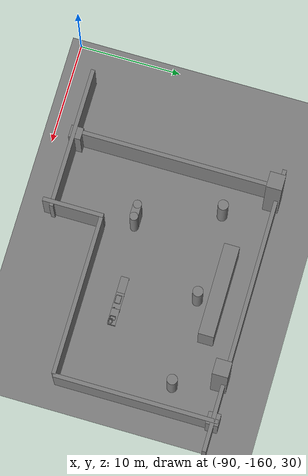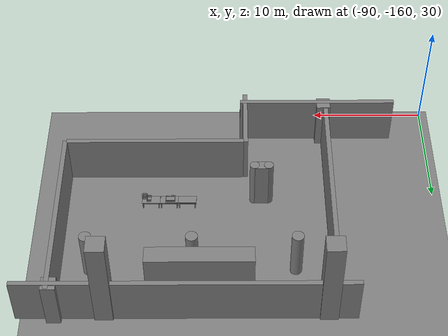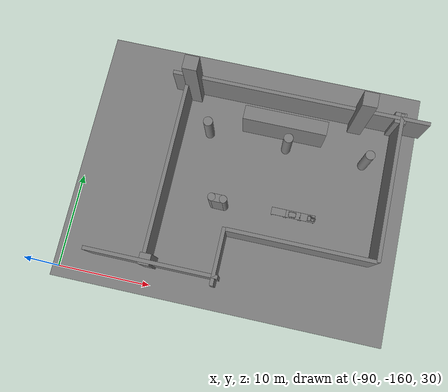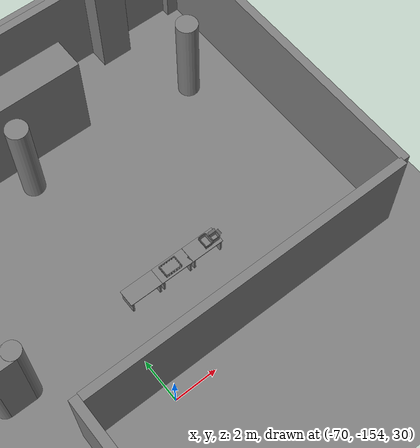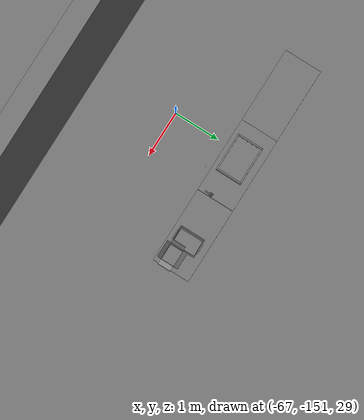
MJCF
<mujoco>
    <option gravity="0.000000000 0.000000000 -9.810000420" timestep="0.0049999999" integrator="implicitfast" density="1.225" viscosity="1.8000001e-05" noslip_iterations="10" iterations="100" sdf_iterations="50">
        <flag multiccd="disable"/>
    </option>
    <size memory="1000M"/>
    <compiler coordinate="local"/>
    <worldbody>
        <light cutoff="30" pos="0 1 1" dir="0 -1 -2"/>
        <light cutoff="30" pos="0 -1 1" dir="0 1 -2"/>
        <body pos="-64.866622925 -149.383972168 30.183746338" euler="89.999992371 89.999946594 0.000000000" name="openloong_gripper_2f85_fix_base_usda_bluebox_01">
            <geom contype="1" conaffinity="1" density="1000" type="box" material="" rgba="0.500000000 0.500000000 0.500000000 1.000000000" solimp="0.899999976 0.949999988 0.001000000" friction="1.000000000 0.005000000 0.000100000" solref="0.020000000 1.000000000" margin="0" condim="3" group="0" pos="0.276596069 0.187225342 0.000061035" quat="0.707107008 0.000077501 0.707106471 0.000077456" size="0.100000001 0.057999998 0.010000000" name="openloong_gripper_2f85_fix_base_usda_geom_BCA3DA28_1546_46E5_8648_3A7CB2CA5C03"/>
            <geom contype="1" conaffinity="1" density="1000" type="box" material="" rgba="0.500000000 0.500000000 0.500000000 1.000000000" solimp="0.899999976 0.949999988 0.001000000" friction="1.000000000 0.005000000 0.000100000" solref="0.020000000 1.000000000" margin="0" condim="3" group="0" pos="0.000000000 0.002883911 0.000000000" quat="1.000000000 0.000000000 0.000000000 0.000000000" size="0.254000008 0.003000000 0.172000006" name="openloong_gripper_2f85_fix_base_usda_geom_6D752F64_2FDC_48F9_AF2D_4B0937CCA0A4"/>
            <geom contype="1" conaffinity="1" density="1000" type="box" material="" rgba="0.500000000 0.500000000 0.500000000 1.000000000" solimp="0.899999976 0.949999988 0.001000000" friction="1.000000000 0.005000000 0.000100000" solref="0.020000000 1.000000000" margin="0" condim="3" group="0" pos="0.000015259 0.124874115 0.173477173" quat="0.999796450 0.020176515 -0.000000015 0.000000030" size="0.259999990 0.119999997 0.007000000" name="openloong_gripper_2f85_fix_base_usda_geom_3A1FF978_27DC_496D_BAD9_BDC21494940E"/>
            <geom contype="1" conaffinity="1" density="1000" type="box" material="" rgba="0.500000000 0.500000000 0.500000000 1.000000000" solimp="0.899999976 0.949999988 0.001000000" friction="1.000000000 0.005000000 0.000100000" solref="0.020000000 1.000000000" margin="0" condim="3" group="0" pos="0.000015259 0.124874115 -0.173477173" quat="0.999796450 -0.020176545 -0.000000015 0.000000000" size="0.259999990 0.119999997 0.007000000" name="openloong_gripper_2f85_fix_base_usda_geom_E9279CCC_E0B0_40C0_9BBC_1BEAA990D1BD"/>
            <geom contype="1" conaffinity="1" density="1000" type="box" material="" rgba="0.500000000 0.500000000 0.500000000 1.000000000" solimp="0.899999976 0.949999988 0.001000000" friction="1.000000000 0.005000000 0.000100000" solref="0.020000000 1.000000000" margin="0" condim="3" group="0" pos="0.000015259 0.214012146 0.188980103" quat="0.999913096 0.013176724 0.000000015 0.000000000" size="0.259999990 0.029999999 0.012500000" name="openloong_gripper_2f85_fix_base_usda_geom_334D66ED_5A7D_4C14_8B2F_19660A49971E"/>
            <geom contype="1" conaffinity="1" density="1000" type="box" material="" rgba="0.500000000 0.500000000 0.500000000 1.000000000" solimp="0.899999976 0.949999988 0.001000000" friction="1.000000000 0.005000000 0.000100000" solref="0.020000000 1.000000000" margin="0" condim="3" group="0" pos="-0.258346558 0.125289917 0.001876831" quat="0.702796996 -0.020792052 0.710783184 0.020769238" size="0.189999998 0.119999997 0.009000000" name="openloong_gripper_2f85_fix_base_usda_geom_04796098_FF43_4E32_AF16_BE2251051CAF"/>
            <geom contype="1" conaffinity="1" density="1000" type="box" material="" rgba="0.500000000 0.500000000 0.500000000 1.000000000" solimp="0.899999976 0.949999988 0.001000000" friction="1.000000000 0.005000000 0.000100000" solref="0.020000000 1.000000000" margin="0" condim="3" group="0" pos="0.000015259 0.214012146 -0.188980103" quat="0.999913096 -0.013176769 0.000000030 0.000000015" size="0.259999990 0.029999999 0.012500000" name="openloong_gripper_2f85_fix_base_usda_geom_74391005_667A_45A3_B76A_0D76AAD72F3F"/>
            <geom contype="1" conaffinity="1" density="1000" type="box" material="" rgba="0.500000000 0.500000000 0.500000000 1.000000000" solimp="0.899999976 0.949999988 0.001000000" friction="1.000000000 0.005000000 0.000100000" solref="0.020000000 1.000000000" margin="0" condim="3" group="0" pos="-0.276596069 0.187225342 0.000061035" quat="0.707106650 0.000077441 0.707106709 0.000077456" size="0.100000001 0.057999998 0.010000000" name="openloong_gripper_2f85_fix_base_usda_geom_38BE0789_4DFC_41DB_9560_DCC5BAE2316A"/>
            <geom contype="1" conaffinity="1" density="1000" type="box" material="" rgba="0.500000000 0.500000000 0.500000000 1.000000000" solimp="0.899999976 0.949999988 0.001000000" friction="1.000000000 0.005000000 0.000100000" solref="0.020000000 1.000000000" margin="0" condim="3" group="0" pos="0.258346558 0.125289917 0.001876831" quat="0.702851534 0.018856451 0.710823834 -0.019329429" size="0.189999998 0.119999997 0.009000000" name="openloong_gripper_2f85_fix_base_usda_geom_70FC7516_061E_402D_9433_EF7DD81307AF"/>
            <freejoint name="openloong_gripper_2f85_fix_base_usda_bluebox_01_joint"/>
            <site size="0.005000000 0.005000000 0.005000000" rgba="0.500000000 0.500000000 0.500000000 1.000000000" pos="0.000000000 0.000000000 0.000000000" quat="0.999961913 0.008726534 0.000000000 0.000000000" group="0" type="sphere" name="openloong_gripper_2f85_fix_base_usda_bluebox_01site"/>
        </body>
        <body pos="-64.496299744 -149.491867065 30.235729218" euler="0.000000000 0.000000000 89.999946594" name="openloong_gripper_2f85_fix_base_usda_cardboardbox_01">
            <geom contype="1" conaffinity="1" density="1000" type="box" material="" rgba="0.500000000 0.500000000 0.500000000 1.000000000" solimp="0.899999976 0.949999988 0.001000000" friction="1.000000000 0.005000000 0.000100000" solref="0.020000000 1.000000000" margin="0" condim="3" group="0" pos="-0.003166199 -0.004086494 0.005052090" quat="1.000000000 0.000000000 0.000000000 0.000000000" size="0.142499998 0.177500010 0.005000000" name="openloong_gripper_2f85_fix_base_usda_geom_41A15217_BB85_4CF9_A232_7D3E80B0A3F6"/>
            <geom contype="1" conaffinity="1" density="1000" type="box" material="" rgba="0.500000000 0.500000000 0.500000000 1.000000000" solimp="0.899999976 0.949999988 0.001000000" friction="1.000000000 0.005000000 0.000100000" solref="0.020000000 1.000000000" margin="0" condim="3" group="0" pos="-0.003166199 0.170316696 0.150570869" quat="1.000000000 0.000000000 0.000000000 0.000000000" size="0.142499998 0.005000000 0.149999991" name="openloong_gripper_2f85_fix_base_usda_geom_FE6D607D_9313_4031_92E0_7A7E70470A1E"/>
            <geom contype="1" conaffinity="1" density="1000" type="box" material="" rgba="0.500000000 0.500000000 0.500000000 1.000000000" solimp="0.899999976 0.949999988 0.001000000" friction="1.000000000 0.005000000 0.000100000" solref="0.020000000 1.000000000" margin="0" condim="3" group="0" pos="-0.147399902 -0.005307198 0.150570869" quat="1.000000000 0.000000000 0.000000000 0.000000000" size="0.005000000 0.177500010 0.149999991" name="openloong_gripper_2f85_fix_base_usda_geom_E024B5FE_B154_4ED7_A7A0_8EEF9F197615"/>
            <geom contype="1" conaffinity="1" density="1000" type="box" material="" rgba="0.500000000 0.500000000 0.500000000 1.000000000" solimp="0.899999976 0.949999988 0.001000000" friction="1.000000000 0.005000000 0.000100000" solref="0.020000000 1.000000000" margin="0" condim="3" group="0" pos="0.140275955 -0.005307198 0.150570869" quat="1.000000000 0.000000000 0.000000000 0.000000000" size="0.005000000 0.177500010 0.149999991" name="openloong_gripper_2f85_fix_base_usda_geom_3BF5B3F5_F58A_44A9_BA6D_F27476240F96"/>
            <geom contype="1" conaffinity="1" density="1000" type="box" material="" rgba="0.500000000 0.500000000 0.500000000 1.000000000" solimp="0.899999976 0.949999988 0.001000000" friction="1.000000000 0.005000000 0.000100000" solref="0.020000000 1.000000000" margin="0" condim="3" group="0" pos="-0.003166199 -0.181550980 0.150570869" quat="1.000000000 0.000000000 0.000000000 0.000000000" size="0.142499998 0.005000000 0.149999991" name="openloong_gripper_2f85_fix_base_usda_geom_B8BC34B0_7057_41AA_A9B9_5BF84F481016"/>
            <freejoint name="openloong_gripper_2f85_fix_base_usda_cardboardbox_01_joint"/>
            <site size="0.005000000 0.005000000 0.005000000" rgba="0.500000000 0.500000000 0.500000000 1.000000000" pos="0.000000000 0.000000000 0.000000000" quat="0.999961913 0.008726535 0.000000000 0.000000000" group="0" type="sphere" name="openloong_gripper_2f85_fix_base_usda_site_50E63006_FED9_48B0_8039_DF6D3855CB40"/>
            <body pos="0.139160156 -0.004048347 0.301930904" euler="-179.999954224 49.383502960 179.999954224" name="openloong_gripper_2f85_fix_base_usda_A1_006">
                <geom contype="1" conaffinity="1" density="1000" type="box" material="" rgba="0.500000000 0.500000000 0.500000000 1.000000000" solimp="0.899999976 0.949999988 0.001000000" friction="1.000000000 0.005000000 0.000100000" solref="0.020000000 1.000000000" margin="0" condim="3" group="0" pos="-0.071587563 0.000009537 0.001745224" quat="0.999999881 0.000000000 0.000000000 0.000000000" size="0.071249999 0.179999992 0.002500000" name="openloong_gripper_2f85_fix_base_usda_geom_AF4197FC_0388_404A_9EA6_BEB13D111A67"/>
                <joint armature="0" stiffness="0.07" damping="0.0099999998" axis="0.000000 1.000000 0.000000" type="hinge" name="openloong_gripper_2f85_fix_base_usda_A1_006"/>
            </body>
            <body pos="-0.145902634 -0.004086494 0.301938057" euler="-180.000000000 -60.000011444 -180.000000000" name="openloong_gripper_2f85_fix_base_usda_A2_006">
                <geom contype="1" conaffinity="1" density="1000" type="box" material="" rgba="0.500000000 0.500000000 0.500000000 1.000000000" solimp="0.899999976 0.949999988 0.001000000" friction="1.000000000 0.005000000 0.000100000" solref="0.020000000 1.000000000" margin="0" condim="3" group="0" pos="0.071268082 0.000009537 0.002717972" quat="0.000002921 0.000000000 -0.000000030 0.999999881" size="0.071249999 0.179999992 0.002500000" name="openloong_gripper_2f85_fix_base_usda_geom_65D041E8_DEE9_4C38_8450_4E31B596C6FB"/>
                <joint armature="0" stiffness="0.07" damping="0.0099999998" axis="0.000000 1.000000 0.000000" type="hinge" name="openloong_gripper_2f85_fix_base_usda_A2_006"/>
            </body>
            <body pos="-0.003385544 0.175991058 0.301930904" euler="-125.858116150 -0.000004561 0.000002331" name="openloong_gripper_2f85_fix_base_usda_B2_006">
                <geom contype="1" conaffinity="1" density="1000" type="box" material="" rgba="0.500000000 0.500000000 0.500000000 1.000000000" solimp="0.899999976 0.949999988 0.001000000" friction="1.000000000 0.005000000 0.000100000" solref="0.020000000 1.000000000" margin="0" condim="3" group="0" pos="0.000009537 -0.070939064 -0.002470016" quat="0.999614120 0.027776197 -0.000000015 0.000000030" size="0.137500003 0.064999998 0.005000000" name="openloong_gripper_2f85_fix_base_usda_geom_A87CE2D0_7AA6_4E01_B173_1EC4AF40F686"/>
                <joint armature="0" stiffness="0.07" damping="0.0099999998" axis="1.000000 0.000000 0.000000" type="hinge" name="openloong_gripper_2f85_fix_base_usda_B2_006"/>
            </body>
            <body pos="-0.003385544 -0.184140205 0.301938057" euler="147.805557251 0.000000000 0.000000000" name="openloong_gripper_2f85_fix_base_usda_B1_006">
                <geom contype="1" conaffinity="1" density="1000" type="box" material="" rgba="0.500000000 0.500000000 0.500000000 1.000000000" solimp="0.899999976 0.949999988 0.001000000" friction="1.000000000 0.005000000 0.000100000" solref="0.020000000 1.000000000" margin="0" condim="3" group="0" pos="-0.000028610 0.070202351 -0.002703667" quat="0.999614179 -0.027776167 0.000000000 0.000000000" size="0.137500003 0.064999998 0.005000000" name="openloong_gripper_2f85_fix_base_usda_geom_C2B5B501_B6E0_4B51_BFA5_D5FC8464EC1B"/>
                <joint armature="0" stiffness="0.07" damping="0.0099999998" axis="1.000000 0.000000 0.000000" type="hinge" name="openloong_gripper_2f85_fix_base_usda_B1_006"/>
            </body>
        </body>
        <body pos="-65.882858276 -149.481979370 30.229999542" euler="-64.487716675 0.000000000 0.000000000" name="openloong_gripper_2f85_fix_base_usda_Barcode">
            <geom contype="1" conaffinity="1" density="1000" type="box" material="" rgba="0.500000000 0.500000000 0.500000000 1.000000000" solimp="0.899999976 0.949999988 0.001000000" friction="1.000000000 0.005000000 0.000100000" solref="0.020000000 1.000000000" margin="0" condim="3" group="0" pos="0.000000000 0.013038635 0.001419067" quat="0.000000000 0.000000000 0.000000000 1.000000119" size="0.034000002 0.010000000 0.017999999" name="openloong_gripper_2f85_fix_base_usda_geom_C24C5734_C6EA_447F_B1CC_822CA18284FB"/>
            <geom contype="1" conaffinity="1" density="1000" type="box" material="" rgba="0.500000000 0.500000000 0.500000000 1.000000000" solimp="0.899999976 0.949999988 0.001000000" friction="1.000000000 0.005000000 0.000100000" solref="0.020000000 1.000000000" margin="0" condim="3" group="0" pos="0.000000000 -0.035301208 -0.007095337" quat="0.000000000 0.000000000 -0.043619365 0.999048233" size="0.028999999 0.010000000 0.020000000" name="openloong_gripper_2f85_fix_base_usda_geom_E2F07E03_0EDA_4A4B_A7D1_11BB2FD75C2E"/>
            <geom contype="1" conaffinity="1" density="1000" type="box" material="" rgba="0.500000000 0.500000000 0.500000000 1.000000000" solimp="0.899999976 0.949999988 0.001000000" friction="1.000000000 0.005000000 0.000100000" solref="0.020000000 1.000000000" margin="0" condim="3" group="0" pos="0.000000000 -0.043411255 -0.011749268" quat="0.922262907 0.386563420 0.000000000 0.000000000" size="0.026000001 0.010000000 0.020000000" name="openloong_gripper_2f85_fix_base_usda_geom_FD110EA2_42E9_4D27_A987_D8F127D17F15"/>
            <geom contype="1" conaffinity="1" density="1000" type="box" material="" rgba="0.500000000 0.500000000 0.500000000 1.000000000" solimp="0.899999976 0.949999988 0.001000000" friction="1.000000000 0.005000000 0.000100000" solref="0.020000000 1.000000000" margin="0" condim="3" group="0" pos="0.000000000 -0.016967773 -0.031860352" quat="0.000000000 0.000000000 0.000000000 1.000000119" size="0.008000000 0.010000000 0.013000000" name="openloong_gripper_2f85_fix_base_usda_geom_0ADEDBA3_054B_4981_AB94_AD2EDDA45E4A"/>
            <geom contype="1" conaffinity="1" density="1000" type="box" material="" rgba="0.500000000 0.500000000 0.500000000 1.000000000" solimp="0.899999976 0.949999988 0.001000000" friction="1.000000000 0.005000000 0.000100000" solref="0.020000000 1.000000000" margin="0" condim="3" group="0" pos="0.000000000 -0.001869202 0.000312805" quat="0.953716993 0.300705761 0.000000000 0.000000000" size="0.032000002 0.010000000 0.018999999" name="openloong_gripper_2f85_fix_base_usda_geom_DAFC682F_6E62_4A8C_9D85_568602811627"/>
            <geom contype="1" conaffinity="1" density="1000" type="box" material="" rgba="0.500000000 0.500000000 0.500000000 1.000000000" solimp="0.899999976 0.949999988 0.001000000" friction="1.000000000 0.005000000 0.000100000" solref="0.020000000 1.000000000" margin="0" condim="3" group="0" pos="0.000000000 -0.019531250 -0.003173828" quat="0.953716993 0.300705761 0.000000000 0.000000000" size="0.030999999 0.010000000 0.020000000" name="openloong_gripper_2f85_fix_base_usda_geom_B72CC592_8A90_4EBF_AAC2_6650582BAB08"/>
            <geom contype="1" conaffinity="1" density="1000" type="box" material="" rgba="0.500000000 0.500000000 0.500000000 1.000000000" solimp="0.899999976 0.949999988 0.001000000" friction="1.000000000 0.005000000 0.000100000" solref="0.020000000 1.000000000" margin="0" condim="3" group="0" pos="0.000000000 -0.035301208 -0.007095337" quat="0.953716993 0.300705761 0.000000000 0.000000000" size="0.028999999 0.010000000 0.020000000" name="openloong_gripper_2f85_fix_base_usda_geom_03BB2F2B_FB51_4557_8DFD_33E4300DB0DF"/>
            <geom contype="1" conaffinity="1" density="1000" type="box" material="" rgba="0.500000000 0.500000000 0.500000000 1.000000000" solimp="0.899999976 0.949999988 0.001000000" friction="1.000000000 0.005000000 0.000100000" solref="0.020000000 1.000000000" margin="0" condim="3" group="0" pos="0.000000000 -0.042617798 -0.071121216" quat="0.000000000 0.000000000 0.000000000 1.000000119" size="0.013000000 0.021000000 0.059999999" name="openloong_gripper_2f85_fix_base_usda_geom_1B20B665_CB08_4EEC_8C29_4795EE57466F"/>
            <freejoint name="openloong_gripper_2f85_fix_base_usda_Barcode_joint"/>
            <site size="0.005000000 0.005000000 0.005000000" rgba="0.500000000 0.500000000 0.500000000 1.000000000" pos="0.000000000 0.000000000 0.000000000" quat="1.000000000 0.000000000 0.000000000 0.000000000" group="0" type="sphere" name="openloong_gripper_2f85_fix_base_usda_Barcode_site"/>
        </body>
        <body pos="-66.745018005 -149.392349243 30.184000015" euler="0.000000000 0.000000000 89.999946594" name="[22329658328760]_Basket_01">
            <geom contype="1" conaffinity="1" density="1000" type="box" material="" rgba="0.500000000 0.500000000 0.500000000 1.000000000" solimp="0.899999976 0.949999988 0.001000000" friction="1.000000000 0.005000000 0.000100000" solref="0.020000000 1.000000000" margin="0" condim="3" group="0" pos="-0.052425385 0.389207840 0.089787483" quat="0.707107008 0.000000000 0.000000000 0.707106411" size="0.014249999 0.014249999 0.059999999" name="[22329658328760]_geom_651FAA6F_6D50_4A55_B888_1D3C6830C132"/>
            <geom contype="1" conaffinity="1" density="1000" type="box" material="" rgba="0.500000000 0.500000000 0.500000000 1.000000000" solimp="0.899999976 0.949999988 0.001000000" friction="1.000000000 0.005000000 0.000100000" solref="0.020000000 1.000000000" margin="0" condim="3" group="0" pos="0.264015198 -0.133043289 0.089787483" quat="0.707107008 0.000000000 0.000000000 0.707106411" size="0.014249999 0.014249999 0.059999999" name="[22329658328760]_geom_9D7FA930_1C85_4BC3_BB21_8037C7407487"/>
            <geom contype="1" conaffinity="1" density="1000" type="box" material="" rgba="0.500000000 0.500000000 0.500000000 1.000000000" solimp="0.899999976 0.949999988 0.001000000" friction="1.000000000 0.005000000 0.000100000" solref="0.020000000 1.000000000" margin="0" condim="3" group="0" pos="-0.264015198 -0.265548706 0.089793205" quat="0.707107008 0.000000000 0.000000000 0.707106411" size="0.014249999 0.014249999 0.059999999" name="[22329658328760]_geom_1323D316_CE88_4C41_AD3D_F305D12EEA2F"/>
            <geom contype="1" conaffinity="1" density="1000" type="box" material="" rgba="0.500000000 0.500000000 0.500000000 1.000000000" solimp="0.899999976 0.949999988 0.001000000" friction="1.000000000 0.005000000 0.000100000" solref="0.020000000 1.000000000" margin="0" condim="3" group="0" pos="-0.160263062 -0.389322281 0.089793205" quat="0.707107008 0.000000000 0.000000000 0.707106411" size="0.014249999 0.014249999 0.059999999" name="[22329658328760]_geom_5722E93F_8478_4A9C_ABA1_D59CCF94AEF2"/>
            <geom contype="1" conaffinity="1" density="1000" type="box" material="" rgba="0.500000000 0.500000000 0.500000000 1.000000000" solimp="0.899999976 0.949999988 0.001000000" friction="1.000000000 0.005000000 0.000100000" solref="0.020000000 1.000000000" margin="0" condim="3" group="0" pos="0.162265778 -0.389322281 0.089787483" quat="0.707107008 0.000000000 0.000000000 0.707106411" size="0.014249999 0.014249999 0.059999999" name="[22329658328760]_geom_2000749A_B8A7_4DE5_9B4D_A4395406F4D8"/>
            <geom contype="1" conaffinity="1" density="1000" type="box" material="" rgba="0.500000000 0.500000000 0.500000000 1.000000000" solimp="0.899999976 0.949999988 0.001000000" friction="1.000000000 0.005000000 0.000100000" solref="0.020000000 1.000000000" margin="0" condim="3" group="0" pos="0.264015198 0.389207840 0.089787483" quat="0.707107008 0.000000000 0.000000000 0.707106411" size="0.014249999 0.014249999 0.059999999" name="[22329658328760]_geom_DABB34E6_EC17_4CDF_935B_C1DC3A420C1D"/>
            <geom contype="1" conaffinity="1" density="1000" type="box" material="" rgba="0.500000000 0.500000000 0.500000000 1.000000000" solimp="0.899999976 0.949999988 0.001000000" friction="1.000000000 0.005000000 0.000100000" solref="0.020000000 1.000000000" margin="0" condim="3" group="0" pos="-0.264015198 -0.133043289 0.089793205" quat="0.707107008 0.000000000 0.000000000 0.707106411" size="0.014249999 0.014249999 0.059999999" name="[22329658328760]_geom_45C1DDDA_4F1B_4E01_B9E7_727E9FEB02E6"/>
            <geom contype="1" conaffinity="1" density="1000" type="box" material="" rgba="0.500000000 0.500000000 0.500000000 1.000000000" solimp="0.899999976 0.949999988 0.001000000" friction="1.000000000 0.005000000 0.000100000" solref="0.020000000 1.000000000" margin="0" condim="3" group="0" pos="-0.264026642 0.269256592 0.089793205" quat="0.707107008 0.000000000 0.000000000 0.707106411" size="0.014249999 0.014249999 0.059999999" name="[22329658328760]_geom_5DDDF4B7_BE95_4B32_BCAA_0066B9FCB53F"/>
            <geom contype="1" conaffinity="1" density="1000" type="box" material="" rgba="0.500000000 0.500000000 0.500000000 1.000000000" solimp="0.899999976 0.949999988 0.001000000" friction="1.000000000 0.005000000 0.000100000" solref="0.020000000 1.000000000" margin="0" condim="3" group="0" pos="0.054462433 0.389207840 0.089787483" quat="0.707107008 0.000000000 0.000000000 0.707106411" size="0.014249999 0.014249999 0.059999999" name="[22329658328760]_geom_062083F7_5AB1_45DD_AFEB_87A3FD4488B7"/>
            <geom contype="1" conaffinity="1" density="1000" type="box" material="" rgba="0.500000000 0.500000000 0.500000000 1.000000000" solimp="0.899999976 0.949999988 0.001000000" friction="1.000000000 0.005000000 0.000100000" solref="0.020000000 1.000000000" margin="0" condim="3" group="0" pos="0.054462433 -0.389322281 0.089787483" quat="0.707107008 0.000000000 0.000000000 0.707106411" size="0.014249999 0.014249999 0.059999999" name="[22329658328760]_geom_3265D584_745D_407E_A76A_EFB57C53220C"/>
            <geom contype="1" conaffinity="1" density="1000" type="box" material="" rgba="0.500000000 0.500000000 0.500000000 1.000000000" solimp="0.899999976 0.949999988 0.001000000" friction="1.000000000 0.005000000 0.000100000" solref="0.020000000 1.000000000" margin="0" condim="3" group="0" pos="0.264015198 0.269256592 0.089793205" quat="0.707107008 0.000000000 0.000000000 0.707106411" size="0.014249999 0.014249999 0.059999999" name="[22329658328760]_geom_0D50F09D_1A76_40AE_9CC4_5D8330619F7B"/>
            <geom contype="1" conaffinity="1" density="1000" type="box" material="" rgba="0.500000000 0.500000000 0.500000000 1.000000000" solimp="0.899999976 0.949999988 0.001000000" friction="1.000000000 0.005000000 0.000100000" solref="0.020000000 1.000000000" margin="0" condim="3" group="0" pos="0.264015198 -0.389322281 0.089787483" quat="0.707107008 0.000000000 0.000000000 0.707106411" size="0.014249999 0.014249999 0.059999999" name="[22329658328760]_geom_3141E791_FE3F_4D6F_B604_9A5FF8157ABC"/>
            <geom contype="1" conaffinity="1" density="1000" type="box" material="" rgba="0.500000000 0.500000000 0.500000000 1.000000000" solimp="0.899999976 0.949999988 0.001000000" friction="1.000000000 0.005000000 0.000100000" solref="0.020000000 1.000000000" margin="0" condim="3" group="0" pos="0.000000000 0.000000000 0.015998840" quat="0.707107008 0.000000000 0.000000000 0.707106411" size="0.403499991 0.279000014 0.015750000" name="[22329658328760]_geom_CD475247_B61D_4802_8578_B5224C00EA1B"/>
            <geom contype="1" conaffinity="1" density="1000" type="box" material="" rgba="0.500000000 0.500000000 0.500000000 1.000000000" solimp="0.899999976 0.949999988 0.001000000" friction="1.000000000 0.005000000 0.000100000" solref="0.020000000 1.000000000" margin="0" condim="3" group="0" pos="0.000000000 -0.389476776 0.163619041" quat="0.707107008 0.000000000 0.000000000 0.707106411" size="0.015000000 0.277500004 0.015750000" name="[22329658328760]_geom_CF480FCA_9C6B_42CE_9897_AC43FBB60AC8"/>
            <geom contype="1" conaffinity="1" density="1000" type="box" material="" rgba="0.500000000 0.500000000 0.500000000 1.000000000" solimp="0.899999976 0.949999988 0.001000000" friction="1.000000000 0.005000000 0.000100000" solref="0.020000000 1.000000000" margin="0" condim="3" group="0" pos="0.162265778 0.389207840 0.089787483" quat="0.707107008 0.000000000 0.000000000 0.707106411" size="0.014249999 0.014249999 0.059999999" name="[22329658328760]_geom_A96060F2_DEE3_410E_AC2A_9166331D9DFC"/>
            <geom contype="1" conaffinity="1" density="1000" type="box" material="" rgba="0.500000000 0.500000000 0.500000000 1.000000000" solimp="0.899999976 0.949999988 0.001000000" friction="1.000000000 0.005000000 0.000100000" solref="0.020000000 1.000000000" margin="0" condim="3" group="0" pos="0.000000000 0.389471054 0.163619041" quat="0.707107008 0.000000000 0.000000000 0.707106411" size="0.015000000 0.277500004 0.015750000" name="[22329658328760]_geom_70381F21_4B0E_4229_8776_9AEF230D0A79"/>
            <geom contype="1" conaffinity="1" density="1000" type="box" material="" rgba="0.500000000 0.500000000 0.500000000 1.000000000" solimp="0.899999976 0.949999988 0.001000000" friction="1.000000000 0.005000000 0.000100000" solref="0.020000000 1.000000000" margin="0" condim="3" group="0" pos="-0.263511658 0.000000000 0.163619041" quat="0.707107008 0.000000000 0.000000000 0.707106411" size="0.403499991 0.015000000 0.015750000" name="[22329658328760]_geom_4E0BA5C5_5DD4_4760_8917_918D5380DDF9"/>
            <geom contype="1" conaffinity="1" density="1000" type="box" material="" rgba="0.500000000 0.500000000 0.500000000 1.000000000" solimp="0.899999976 0.949999988 0.001000000" friction="1.000000000 0.005000000 0.000100000" solref="0.020000000 1.000000000" margin="0" condim="3" group="0" pos="-0.264015198 0.141334534 0.089793205" quat="0.707107008 0.000000000 0.000000000 0.707106411" size="0.014249999 0.014249999 0.059999999" name="[22329658328760]_geom_FB1A19E0_43B5_4EFF_8BEE_8AEC6A235B77"/>
            <geom contype="1" conaffinity="1" density="1000" type="box" material="" rgba="0.500000000 0.500000000 0.500000000 1.000000000" solimp="0.899999976 0.949999988 0.001000000" friction="1.000000000 0.005000000 0.000100000" solref="0.020000000 1.000000000" margin="0" condim="3" group="0" pos="0.264015198 -0.265548706 0.089787483" quat="0.707107008 0.000000000 0.000000000 0.707106411" size="0.014249999 0.014249999 0.059999999" name="[22329658328760]_geom_563BFFBF_3F79_4079_96F5_77B40414ADF3"/>
            <geom contype="1" conaffinity="1" density="1000" type="box" material="" rgba="0.500000000 0.500000000 0.500000000 1.000000000" solimp="0.899999976 0.949999988 0.001000000" friction="1.000000000 0.005000000 0.000100000" solref="0.020000000 1.000000000" margin="0" condim="3" group="0" pos="-0.160263062 0.389207840 0.089787483" quat="0.707107008 0.000000000 0.000000000 0.707106411" size="0.014249999 0.014249999 0.059999999" name="[22329658328760]_geom_CB972D18_8D26_46CC_833A_F1DBC4DE8E50"/>
            <geom contype="1" conaffinity="1" density="1000" type="box" material="" rgba="0.500000000 0.500000000 0.500000000 1.000000000" solimp="0.899999976 0.949999988 0.001000000" friction="1.000000000 0.005000000 0.000100000" solref="0.020000000 1.000000000" margin="0" condim="3" group="0" pos="-0.052425385 -0.389322281 0.089787483" quat="0.707107008 0.000000000 0.000000000 0.707106411" size="0.014249999 0.014249999 0.059999999" name="[22329658328760]_geom_DD8764B0_52BC_4572_8362_B24C5B24C57C"/>
            <geom contype="1" conaffinity="1" density="1000" type="box" material="" rgba="0.500000000 0.500000000 0.500000000 1.000000000" solimp="0.899999976 0.949999988 0.001000000" friction="1.000000000 0.005000000 0.000100000" solref="0.020000000 1.000000000" margin="0" condim="3" group="0" pos="-0.264026642 -0.389322281 0.089793205" quat="0.707107008 0.000000000 0.000000000 0.707106411" size="0.014249999 0.014249999 0.059999999" name="[22329658328760]_geom_F39C3B97_C234_4A0C_9B29_E14B9DBE13CE"/>
            <geom contype="1" conaffinity="1" density="1000" type="box" material="" rgba="0.500000000 0.500000000 0.500000000 1.000000000" solimp="0.899999976 0.949999988 0.001000000" friction="1.000000000 0.005000000 0.000100000" solref="0.020000000 1.000000000" margin="0" condim="3" group="0" pos="0.264015198 0.141334534 0.089787483" quat="0.707107008 0.000000000 0.000000000 0.707106411" size="0.014249999 0.014249999 0.059999999" name="[22329658328760]_geom_B6D67069_D7FE_420C_A9F2_9F000B03DDEE"/>
            <geom contype="1" conaffinity="1" density="1000" type="box" material="" rgba="0.500000000 0.500000000 0.500000000 1.000000000" solimp="0.899999976 0.949999988 0.001000000" friction="1.000000000 0.005000000 0.000100000" solref="0.020000000 1.000000000" margin="0" condim="3" group="0" pos="-0.264015198 0.389207840 0.089793205" quat="0.707107008 0.000000000 0.000000000 0.707106411" size="0.014249999 0.014249999 0.059999999" name="[22329658328760]_geom_92E46096_52FA_4706_AC5E_5D77F78CA9D2"/>
            <geom contype="1" conaffinity="1" density="1000" type="box" material="" rgba="0.500000000 0.500000000 0.500000000 1.000000000" solimp="0.899999976 0.949999988 0.001000000" friction="1.000000000 0.005000000 0.000100000" solref="0.020000000 1.000000000" margin="0" condim="3" group="0" pos="0.264015198 0.004480362 0.089787483" quat="0.707107008 0.000000000 0.000000000 0.707106411" size="0.014249999 0.014249999 0.059999999" name="[22329658328760]_geom_05600DE8_7A0E_4195_B391_04E2C2200FEB"/>
            <geom contype="1" conaffinity="1" density="1000" type="box" material="" rgba="0.500000000 0.500000000 0.500000000 1.000000000" solimp="0.899999976 0.949999988 0.001000000" friction="1.000000000 0.005000000 0.000100000" solref="0.020000000 1.000000000" margin="0" condim="3" group="0" pos="0.263694763 -0.000011444 0.163619041" quat="0.707107008 0.000000000 0.000000000 0.707106411" size="0.403499991 0.015000000 0.015750000" name="[22329658328760]_geom_C1EE270C_1F37_489F_B5D3_13F879B04FBE"/>
            <geom contype="1" conaffinity="1" density="1000" type="box" material="" rgba="0.500000000 0.500000000 0.500000000 1.000000000" solimp="0.899999976 0.949999988 0.001000000" friction="1.000000000 0.005000000 0.000100000" solref="0.020000000 1.000000000" margin="0" condim="3" group="0" pos="-0.264015198 0.004480362 0.089793205" quat="0.707107008 0.000000000 0.000000000 0.707106411" size="0.014249999 0.014249999 0.059999999" name="[22329658328760]_geom_A676CBA1_1A9F_4E27_8A20_41F9E83144DA"/>
            <freejoint name="[22329658328760]_joint_4DC8AA27_2994_49C6_9DA1_7F67375C64C6"/>
        </body>
        <body pos="0.000000000 0.000000000 0.000000000" euler="0.000000000 0.000000000 0.000000000" name="Static Objects_Static Objects">
            <geom contype="1" conaffinity="1" density="1000" type="box" material="" rgba="0.500000000 0.500000000 0.500000000 1.000000000" solimp="0.899999976 0.949999988 0.001000000" friction="1.000000000 0.005000000 0.000100000" solref="0.020000000 1.000000000" margin="0" condim="3" group="0" pos="-67.544113159 -149.365814209 29.727830887" quat="0.500000417 0.499999970 0.499999553 0.499999970" size="0.381000012 0.319999993 0.041000001" name="Static Objects_geom_2B0B4C43_7861_41CC_AD6F_747BA55A7A21"/>
            <geom contype="1" conaffinity="1" density="1000" type="box" material="" rgba="0.500000000 0.500000000 0.500000000 1.000000000" solimp="0.899999976 0.949999988 0.001000000" friction="1.000000000 0.005000000 0.000100000" solref="0.020000000 1.000000000" margin="0" condim="3" group="0" pos="-68.239501953 -149.365814209 30.086868286" quat="0.500000417 0.499999970 0.499999553 0.499999970" size="0.370999992 0.039500002 0.745000005" name="Static Objects_geom_1459CB41_9D64_47FF_9B6F_E5AF1698B2E1"/>
            <geom contype="1" conaffinity="1" density="1000" type="box" material="" rgba="0.500000000 0.500000000 0.500000000 1.000000000" solimp="0.899999976 0.949999988 0.001000000" friction="1.000000000 0.005000000 0.000100000" solref="0.020000000 1.000000000" margin="0" condim="3" group="0" pos="-68.239501953 -149.365814209 30.147235870" quat="0.500000417 0.499999970 0.499999553 0.499999970" size="0.400000006 0.022000000 0.800000012" name="Static Objects_geom_3EB9E159_7A77_410C_97BF_B58370C4868B"/>
            <geom contype="1" conaffinity="1" density="1000" type="box" material="" rgba="0.500000000 0.500000000 0.500000000 1.000000000" solimp="0.899999976 0.949999988 0.001000000" friction="1.000000000 0.005000000 0.000100000" solref="0.020000000 1.000000000" margin="0" condim="3" group="0" pos="-68.934890747 -149.365814209 29.727830887" quat="0.500000417 0.499999970 0.499999553 0.499999970" size="0.381000012 0.319999993 0.041000001" name="Static Objects_geom_4C8B51C6_D481_4A65_B808_4C277A0FE925"/>
            <geom contype="1" conaffinity="1" density="1000" type="box" material="" rgba="0.500000000 0.500000000 0.500000000 1.000000000" solimp="0.899999976 0.949999988 0.001000000" friction="1.000000000 0.005000000 0.000100000" solref="0.020000000 1.000000000" margin="0" condim="3" group="0" pos="-68.239501953 -149.365814209 29.561563492" quat="0.500000417 0.499999970 0.499999553 0.499999970" size="0.020000000 0.022000000 0.660000026" name="Static Objects_geom_BC75A39C_3400_4270_8E5E_8DA9F4A6B026"/>
            <geom contype="1" conaffinity="1" density="1000" type="box" material="" rgba="0.500000000 0.500000000 0.500000000 1.000000000" solimp="0.899999976 0.949999988 0.001000000" friction="1.000000000 0.005000000 0.000100000" solref="0.020000000 1.000000000" margin="0" condim="3" group="0" pos="-65.945671082 -149.365814209 29.727830887" quat="0.500000417 0.499999970 0.499999553 0.499999970" size="0.381000012 0.319999993 0.041000001" name="Static Objects_geom_CE33A957_9363_4320_9FB3_46347C0E4DA6"/>
            <geom contype="1" conaffinity="1" density="1000" type="box" material="" rgba="0.500000000 0.500000000 0.500000000 1.000000000" solimp="0.899999976 0.949999988 0.001000000" friction="1.000000000 0.005000000 0.000100000" solref="0.020000000 1.000000000" margin="0" condim="3" group="0" pos="-66.641059875 -149.365814209 30.086868286" quat="0.500000417 0.499999970 0.499999553 0.499999970" size="0.370999992 0.039500002 0.745000005" name="Static Objects_geom_6090A68A_571C_46B6_A559_4DE919449EAE"/>
            <geom contype="1" conaffinity="1" density="1000" type="box" material="" rgba="0.500000000 0.500000000 0.500000000 1.000000000" solimp="0.899999976 0.949999988 0.001000000" friction="1.000000000 0.005000000 0.000100000" solref="0.020000000 1.000000000" margin="0" condim="3" group="0" pos="-66.641059875 -149.365814209 30.147235870" quat="0.500000417 0.499999970 0.499999553 0.499999970" size="0.400000006 0.022000000 0.800000012" name="Static Objects_geom_26E50689_0493_4461_B80F_7DC7EAC193D3"/>
            <geom contype="1" conaffinity="1" density="1000" type="box" material="" rgba="0.500000000 0.500000000 0.500000000 1.000000000" solimp="0.899999976 0.949999988 0.001000000" friction="1.000000000 0.005000000 0.000100000" solref="0.020000000 1.000000000" margin="0" condim="3" group="0" pos="-67.336448669 -149.365814209 29.727830887" quat="0.500000417 0.499999970 0.499999553 0.499999970" size="0.381000012 0.319999993 0.041000001" name="Static Objects_geom_A4E16995_D9EB_4B0C_ABCB_E3F284585850"/>
            <geom contype="1" conaffinity="1" density="1000" type="box" material="" rgba="0.500000000 0.500000000 0.500000000 1.000000000" solimp="0.899999976 0.949999988 0.001000000" friction="1.000000000 0.005000000 0.000100000" solref="0.020000000 1.000000000" margin="0" condim="3" group="0" pos="-66.641059875 -149.365814209 29.561563492" quat="0.500000417 0.499999970 0.499999553 0.499999970" size="0.020000000 0.022000000 0.660000026" name="Static Objects_geom_B21E524F_FC42_4D97_AE7F_21C4B935B54B"/>
            <geom contype="1" conaffinity="1" density="1000" type="box" material="" rgba="0.500000000 0.500000000 0.500000000 1.000000000" solimp="0.899999976 0.949999988 0.001000000" friction="1.000000000 0.005000000 0.000100000" solref="0.020000000 1.000000000" margin="0" condim="3" group="0" pos="-64.338577271 -149.365814209 29.727830887" quat="0.500000417 0.499999970 0.499999553 0.499999970" size="0.381000012 0.319999993 0.041000001" name="Static Objects_geom_06CBDAC6_2501_413C_9406_B22FF7B1F9AE"/>
            <geom contype="1" conaffinity="1" density="1000" type="box" material="" rgba="0.500000000 0.500000000 0.500000000 1.000000000" solimp="0.899999976 0.949999988 0.001000000" friction="1.000000000 0.005000000 0.000100000" solref="0.020000000 1.000000000" margin="0" condim="3" group="0" pos="-65.033966064 -149.365814209 30.086868286" quat="0.500000417 0.499999970 0.499999553 0.499999970" size="0.370999992 0.039500002 0.745000005" name="Static Objects_geom_40277E41_EAB8_4202_B52C_0ACC96921C13"/>
            <geom contype="1" conaffinity="1" density="1000" type="box" material="" rgba="0.500000000 0.500000000 0.500000000 1.000000000" solimp="0.899999976 0.949999988 0.001000000" friction="1.000000000 0.005000000 0.000100000" solref="0.020000000 1.000000000" margin="0" condim="3" group="0" pos="-65.033966064 -149.365814209 30.147235870" quat="0.500000417 0.499999970 0.499999553 0.499999970" size="0.400000006 0.022000000 0.800000012" name="Static Objects_geom_5AF2FBE4_283E_407E_8AED_D26042C6C4A9"/>
            <geom contype="1" conaffinity="1" density="1000" type="box" material="" rgba="0.500000000 0.500000000 0.500000000 1.000000000" solimp="0.899999976 0.949999988 0.001000000" friction="1.000000000 0.005000000 0.000100000" solref="0.020000000 1.000000000" margin="0" condim="3" group="0" pos="-65.729354858 -149.365814209 29.727830887" quat="0.500000417 0.499999970 0.499999553 0.499999970" size="0.381000012 0.319999993 0.041000001" name="Static Objects_geom_C78E1371_DEEC_46EF_AD72_58363B9101A3"/>
            <geom contype="1" conaffinity="1" density="1000" type="box" material="" rgba="0.500000000 0.500000000 0.500000000 1.000000000" solimp="0.899999976 0.949999988 0.001000000" friction="1.000000000 0.005000000 0.000100000" solref="0.020000000 1.000000000" margin="0" condim="3" group="0" pos="-65.033966064 -149.365814209 29.561563492" quat="0.500000417 0.499999970 0.499999553 0.499999970" size="0.020000000 0.022000000 0.660000026" name="Static Objects_geom_3D93187C_6DF2_4484_AAFB_A59EF85CC7FB"/>
            <geom contype="1" conaffinity="1" density="1000" type="box" material="" rgba="0.500000000 0.500000000 0.500000000 1.000000000" solimp="0.899999976 0.949999988 0.001000000" friction="1.000000000 0.005000000 0.000100000" solref="0.020000000 1.000000000" margin="0" condim="3" group="0" pos="-61.754566193 -137.853729248 33.906845093" quat="0.707107067 0.000000000 0.000000000 0.707106471" size="0.759999990 0.759999990 4.500000000" name="Static Objects_geom_663C1FF5_66CF_4FF5_B605_825DF530B165"/>
            <geom contype="1" conaffinity="1" density="1000" type="box" material="" rgba="0.500000000 0.500000000 0.500000000 1.000000000" solimp="0.899999976 0.949999988 0.001000000" friction="1.000000000 0.005000000 0.000100000" solref="0.020000000 1.000000000" margin="0" condim="3" group="0" pos="-57.511135101 -144.927108765 31.707921982" quat="1.000000000 0.000000000 0.000000000 0.000000000" size="0.200000003 8.000000000 2.299999952" name="Static Objects_geom_915F936B_D7ED_4F24_85D4_5A34E249BE95"/>
            <geom contype="1" conaffinity="1" density="1000" type="box" material="" rgba="0.500000000 0.500000000 0.500000000 1.000000000" solimp="0.899999976 0.949999988 0.001000000" friction="1.000000000 0.005000000 0.000100000" solref="0.020000000 1.000000000" margin="0" condim="3" group="0" pos="-80.517646790 -157.574050903 31.688196182" quat="0.707107067 0.000000000 0.000000000 0.707106471" size="0.600000024 0.600000024 2.299999952" name="Static Objects_geom_012412EE_44E7_402A_ADD4_DC1C718F06BF"/>
            <geom contype="1" conaffinity="1" density="1000" type="box" material="" rgba="0.500000000 0.500000000 0.500000000 1.000000000" solimp="0.899999976 0.949999988 0.001000000" friction="1.000000000 0.005000000 0.000100000" solref="0.020000000 1.000000000" margin="0" condim="3" group="0" pos="-80.711044312 -147.414932251 31.666158676" quat="1.000000000 0.000000000 0.000000000 0.000000000" size="0.200000003 10.000000000 2.299999952" name="Static Objects_geom_26D20CA1_84B3_4C92_B91E_1904161BD0B7"/>
            <geom contype="1" conaffinity="1" density="1000" type="box" material="" rgba="0.500000000 0.500000000 0.500000000 1.000000000" solimp="0.899999976 0.949999988 0.001000000" friction="1.000000000 0.005000000 0.000100000" solref="0.020000000 1.000000000" margin="0" condim="3" group="0" pos="-57.687217712 -137.434692383 31.688196182" quat="0.707107067 0.000000000 0.000000000 0.707106471" size="0.600000024 0.600000024 2.299999952" name="Static Objects_geom_9DCDC1E9_21C5_448B_BFF5_D08C2B8DC192"/>
            <geom contype="1" conaffinity="1" density="1000" type="box" material="" rgba="0.500000000 0.500000000 0.500000000 1.000000000" solimp="0.899999976 0.949999988 0.001000000" friction="1.000000000 0.005000000 0.000100000" solref="0.020000000 1.000000000" margin="0" condim="3" group="0" pos="-69.537033081 -140.263229370 31.714921951" quat="0.707107067 0.000000000 0.000000000 0.707106471" size="0.759999990 4.500000000 2.299999952" name="Static Objects_geom_DFEB2A5F_92C3_4F5D_BBBA_F72DB80582F5"/>
            <geom contype="1" conaffinity="1" density="1000" type="box" material="" rgba="0.500000000 0.500000000 0.500000000 1.000000000" solimp="0.899999976 0.949999988 0.001000000" friction="1.000000000 0.005000000 0.000100000" solref="0.020000000 1.000000000" margin="0" condim="3" group="0" pos="-80.073638916 -137.853713989 33.906845093" quat="0.707107067 0.000000000 0.000000000 0.707106471" size="0.759999990 0.759999990 4.500000000" name="Static Objects_geom_BF1B1FDE_DA1A_4472_932F_ED3E66F45D0E"/>
            <geom contype="1" conaffinity="1" density="1000" type="box" material="" rgba="0.500000000 0.500000000 0.500000000 1.000000000" solimp="0.899999976 0.949999988 0.001000000" friction="1.000000000 0.005000000 0.000100000" solref="0.020000000 1.000000000" margin="0" condim="3" group="0" pos="-73.406707764 -155.734664917 31.707921982" quat="1.000000000 0.000000000 0.000000000 0.000000000" size="0.200000003 3.000000000 2.299999952" name="Static Objects_geom_0C1D8F07_1F1C_4D0D_817D_7E7A2BC54259"/>
            <geom contype="1" conaffinity="1" density="1000" type="box" material="" rgba="0.500000000 0.500000000 0.500000000 1.000000000" solimp="0.899999976 0.949999988 0.001000000" friction="1.000000000 0.005000000 0.000100000" solref="0.020000000 1.000000000" margin="0" condim="3" group="0" pos="-68.497543335 -137.448257446 31.707921982" quat="0.707107067 0.000000000 0.000000000 0.707106471" size="0.200000003 14.000000000 2.299999952" name="Static Objects_geom_2044747A_7284_4762_9D68_6F1FD6BFDAFC"/>
            <geom contype="1" conaffinity="1" density="1000" type="cylinder" material="" rgba="0.500000000 0.500000000 0.500000000 1.000000000" solimp="0.899999976 0.949999988 0.001000000" friction="1.000000000 0.005000000 0.000100000" solref="0.020000000 1.000000000" margin="0" condim="3" group="0" pos="-68.868522644 -142.134506226 31.711090088" quat="0.707107067 0.000000000 0.000000000 0.707106471" size="0.509999990 2.299999952 1.000000000" name="Static Objects_geom_BD4F133A_1FF9_4EB4_AB69_81C71117D6B5"/>
            <geom contype="1" conaffinity="1" density="1000" type="plane" material="" rgba="0.500000000 0.500000000 0.500000000 1.000000000" solimp="0.899999976 0.949999988 0.001000000" friction="1.000000000 0.005000000 0.000100000" solref="0.020000000 1.000000000" margin="0" condim="3" group="0" pos="-72.873703003 -147.131927490 29.409669876" quat="1.000000000 0.000000000 0.000000000 0.000000000" size="18.000000000 14.000000000 1.000000000" name="Static Objects_geom_944C56F5_73E2_412A_981C_AE35786F8044"/>
            <geom contype="1" conaffinity="1" density="1000" type="box" material="" rgba="0.500000000 0.500000000 0.500000000 1.000000000" solimp="0.899999976 0.949999988 0.001000000" friction="1.000000000 0.005000000 0.000100000" solref="0.020000000 1.000000000" margin="0" condim="3" group="0" pos="-79.943580627 -157.782272339 31.707921982" quat="0.707107067 0.000000000 0.000000000 0.707106471" size="0.200000003 7.000000000 2.299999952" name="Static Objects_geom_6F21BF15_3E1B_41D0_A86C_A96637E7611E"/>
            <geom contype="1" conaffinity="1" density="1000" type="box" material="" rgba="0.500000000 0.500000000 0.500000000 1.000000000" solimp="0.899999976 0.949999988 0.001000000" friction="1.000000000 0.005000000 0.000100000" solref="0.020000000 1.000000000" margin="0" condim="3" group="0" pos="-65.421028137 -152.903442383 31.707921982" quat="0.707107067 0.000000000 0.000000000 0.707106471" size="0.200000003 7.800000191 2.299999952" name="Static Objects_geom_BCEF81A5_DA4B_461B_A217_38B137A39F54"/>
            <geom contype="1" conaffinity="1" density="1000" type="box" material="" rgba="0.500000000 0.500000000 0.500000000 1.000000000" solimp="0.899999976 0.949999988 0.001000000" friction="1.000000000 0.005000000 0.000100000" solref="0.020000000 1.000000000" margin="0" condim="3" group="0" pos="-74.776908875 -149.964416504 31.688196182" quat="1.000000000 0.000000000 0.000000000 0.000000000" size="0.600000024 0.409999996 2.299999952" name="Static Objects_geom_68DB4734_4581_4A81_BB21_E40D934A9E4F"/>
            <geom contype="1" conaffinity="1" density="1000" type="cylinder" material="" rgba="0.500000000 0.500000000 0.500000000 1.000000000" solimp="0.899999976 0.949999988 0.001000000" friction="1.000000000 0.005000000 0.000100000" solref="0.020000000 1.000000000" margin="0" condim="3" group="0" pos="-60.161884308 -142.134506226 31.711090088" quat="0.707107067 0.000000000 0.000000000 0.707106471" size="0.509999990 2.299999952 1.000000000" name="Static Objects_geom_5260B73E_D44F_4D15_B203_404859CCAD45"/>
            <geom contype="1" conaffinity="1" density="1000" type="cylinder" material="" rgba="0.500000000 0.500000000 0.500000000 1.000000000" solimp="0.899999976 0.949999988 0.001000000" friction="1.000000000 0.005000000 0.000100000" solref="0.020000000 1.000000000" margin="0" condim="3" group="0" pos="-75.382453918 -149.963455200 31.711090088" quat="0.707107067 0.000000000 0.000000000 0.707106471" size="0.409999996 2.299999952 1.000000000" name="Static Objects_geom_6A5E6ECE_C0CC_45A8_9B3D_2EEAEF4B5F75"/>
            <geom contype="1" conaffinity="1" density="1000" type="cylinder" material="" rgba="0.500000000 0.500000000 0.500000000 1.000000000" solimp="0.899999976 0.949999988 0.001000000" friction="1.000000000 0.005000000 0.000100000" solref="0.020000000 1.000000000" margin="0" condim="3" group="0" pos="-74.154960632 -149.963455200 31.711090088" quat="0.707107067 0.000000000 0.000000000 0.707106471" size="0.409999996 2.299999952 1.000000000" name="Static Objects_geom_B07B31ED_020B_4EDC_AFE1_9B830FE27725"/>
            <geom contype="1" conaffinity="1" density="1000" type="cylinder" material="" rgba="0.500000000 0.500000000 0.500000000 1.000000000" solimp="0.899999976 0.949999988 0.001000000" friction="1.000000000 0.005000000 0.000100000" solref="0.020000000 1.000000000" margin="0" condim="3" group="0" pos="-77.566612244 -142.134506226 31.711090088" quat="0.707107067 0.000000000 0.000000000 0.707106471" size="0.509999990 2.299999952 1.000000000" name="Static Objects_geom_606C3FDB_F995_4BC5_A6E3_51CAFD4B8EEB"/>
        </body>
        <body pos="-66.291030884 -149.869689941 29.018842697" euler="0.000000000 0.000000000 89.999946594" mocap="true" name="openloong_gripper_2f85_fix_base_usda_leftHandMocap"/>
        <body pos="-66.291030884 -149.869689941 29.018842697" euler="0.000000000 0.000000000 89.999946594" mocap="true" name="openloong_gripper_2f85_fix_base_usda_rightHandMocap"/>
        <body pos="-66.291030884 -149.869689941 30.218843460" euler="0.000000000 0.000000000 89.999946594" name="openloong_gripper_2f85_fix_base_usda_base_link">
            <geom contype="1" conaffinity="1" density="1000" type="mesh" material="" rgba="0.783999979 0.783999979 0.783999979 1.000000000" solimp="0.899999976 0.949999988 0.001000000" friction="1.000000000 0.005000000 0.000100000" solref="0.020000000 1.000000000" margin="0" condim="3" group="3" mesh="base_link" pos="0.000000000 0.000000000 0.000000000" quat="1.000000000 0.000000000 0.000000000 0.000000000" size="1.000000000 1.000000000 1.000000000" name="openloong_gripper_2f85_fix_base_usda__geom_7_103574B0_297B_40FD_AB94_E8E73B7F4151"/>
            <site size="0.005000000 0.005000000 0.005000000" rgba="0.500000000 0.500000000 0.500000000 1.000000000" pos="0.000000000 0.000000000 0.000000000" quat="1.000000000 0.000000000 0.000000000 0.000000000" group="0" type="sphere" name="openloong_gripper_2f85_fix_base_usda_imu"/>
            <inertial mass="22.447001" pos="-0.005664100 -0.001336700 0.238289997" diaginertia="0.374352545 0.277180195 0.220617250" quat="0.999247074 0.035235517 -0.015086859 0.006023135"/>
            <body pos="0.000000000 0.000000000 0.299997330" euler="0.000000000 0.000000000 0.000000000" name="openloong_gripper_2f85_fix_base_usda_dummy_body">
                <geom contype="1" conaffinity="1" density="1000" type="sphere" material="" rgba="0.783999979 0.783999979 0.783999979 1.000000000" solimp="0.899999976 0.949999988 0.001000000" friction="1.000000000 0.005000000 0.000100000" solref="0.020000000 1.000000000" margin="0" condim="3" group="3" pos="0.000000000 0.000000000 0.000000000" quat="1.000000000 0.000000000 0.000000000 0.000000000" size="0.010000000 0.000000000 0.000000000" name="openloong_gripper_2f85_fix_base_usda__geom_8_36B35FBE_C81D_43D1_A5D8_C75EF8E04BE6"/>
                <joint armature="0.0099999998" stiffness="0" damping="0.1" axis="0.000000 0.000000 1.000000" type="hinge" name="openloong_gripper_2f85_fix_base_usda_dummy_joint"/>
                <site size="0.010000000 0.005000000 0.005000000" rgba="0.500000000 0.500000000 0.500000000 1.000000000" pos="0.000000000 0.000000000 0.000000000" quat="1.000000000 0.000000000 0.000000000 0.000000000" group="3" type="sphere" name="openloong_gripper_2f85_fix_base_usda_dummy_site"/>
            </body>
            <body pos="0.009002686 0.000000000 0.406400681" euler="0.000000000 0.000000000 0.000000000" name="openloong_gripper_2f85_fix_base_usda_Link_head_yaw">
                <geom contype="1" conaffinity="1" density="1000" type="mesh" material="" rgba="0.783999979 0.783999979 0.783999979 1.000000000" solimp="0.899999976 0.949999988 0.001000000" friction="1.000000000 0.005000000 0.000100000" solref="0.020000000 1.000000000" margin="0" condim="3" group="3" mesh="Link_head_yaw" pos="0.000000000 0.000000000 0.000000000" quat="1.000000000 0.000000000 0.000000000 0.000000000" size="1.000000000 1.000000000 1.000000000" name="openloong_gripper_2f85_fix_base_usda__geom_10_07069C46_59AD_4F85_B729_95B19BA460B0"/>
                <inertial mass="0.84249002" pos="0.000000000 -0.002081400 0.044801001" diaginertia="0.000700588 0.000629000 0.000553812" quat="0.706933022 -0.015675601 0.015677100 0.706933022"/>
                <body pos="0.000000000 -0.034599304 0.048500061" euler="0.000000000 0.000000000 0.000000000" name="openloong_gripper_2f85_fix_base_usda_Link_head_pitch">
                    <geom contype="1" conaffinity="1" density="1000" type="mesh" material="" rgba="0.783999979 0.783999979 0.783999979 1.000000000" solimp="0.899999976 0.949999988 0.001000000" friction="1.000000000 0.005000000 0.000100000" solref="0.020000000 1.000000000" margin="0" condim="3" group="3" mesh="Link_head_pitch" pos="0.000000000 0.000000000 0.000000000" quat="1.000000000 0.000000000 0.000000000 0.000000000" size="1.000000000 1.000000000 1.000000000" name="openloong_gripper_2f85_fix_base_usda__geom_12_6E9C5E49_A20B_41E1_ADC9_5FE0B66D35AF"/>
                    <inertial mass="1.3943" pos="0.020569000 0.033004001 0.125000000" diaginertia="0.006381400 0.006289940 0.004481460" quat="0.973390222 0.008406822 0.228157058 0.019624906"/>
                    <body pos="0.000000000 0.029998779 0.000000000" euler="0.000000000 0.000000000 0.000000000" name="openloong_gripper_2f85_fix_base_usda_neck_center_body">
                        <site size="0.010000000 0.005000000 0.005000000" rgba="0.500000000 0.500000000 0.500000000 1.000000000" pos="0.000000000 0.000000000 0.000000000" quat="1.000000000 0.000000000 0.000000000 0.000000000" group="3" type="sphere" name="openloong_gripper_2f85_fix_base_usda_neck_center_site"/>
                        <body pos="0.020004272 0.000000000 0.149999619" euler="-0.000002229 39.998176575 -90.000205994" name="openloong_gripper_2f85_fix_base_usda_camera_head">
                            <site size="0.010000000 0.005000000 0.005000000" rgba="0.500000000 0.500000000 0.500000000 1.000000000" pos="0.000000000 0.000000000 0.000000000" quat="1.000000000 0.000000000 0.000000000 0.000000000" group="3" type="sphere" name="openloong_gripper_2f85_fix_base_usda_camera_head_site"/>
                        </body>
                    </body>
                </body>
            </body>
            <body pos="0.003997803 -0.161598206 0.392200470" euler="0.000000000 0.000000000 0.000000000" name="openloong_gripper_2f85_fix_base_usda_Link_arm_r_01">
                <geom contype="1" conaffinity="1" density="1000" type="mesh" material="" rgba="0.783999979 0.783999979 0.783999979 1.000000000" solimp="0.899999976 0.949999988 0.001000000" friction="1.000000000 0.005000000 0.000100000" solref="0.020000000 1.000000000" margin="0" condim="3" group="3" mesh="Link_arm_r_01" pos="0.000000000 0.000000000 0.000000000" quat="1.000000000 0.000000000 0.000000000 0.000000000" size="1.000000000 1.000000000 1.000000000" name="openloong_gripper_2f85_fix_base_usda__geom_14_166FC83F_B029_4818_8D43_CA25E7D4FC87"/>
                <joint armature="0.0099999998" stiffness="0" damping="1" axis="0.000000 -1.000000 0.000000" limited="true" range="-170.000015259 170.000015259" type="hinge" name="openloong_gripper_2f85_fix_base_usda_J_arm_r_01"/>
                <inertial mass="0.75641" pos="0.004494600 -0.038293999 -0.000001874" diaginertia="0.000842990 0.000803050 0.000587120" quat="-0.000163502 0.707098067 0.000812463 0.707115054"/>
                <body pos="-0.041992188 -0.041000366 0.000000000" euler="0.000000000 0.000000000 0.000000000" name="openloong_gripper_2f85_fix_base_usda_Link_arm_r_02">
                    <geom contype="1" conaffinity="1" density="1000" type="mesh" material="" rgba="0.783999979 0.783999979 0.783999979 1.000000000" solimp="0.899999976 0.949999988 0.001000000" friction="1.000000000 0.005000000 0.000100000" solref="0.020000000 1.000000000" margin="0" condim="3" group="3" mesh="Link_arm_r_02" pos="0.000000000 0.000000000 0.000000000" quat="1.000000000 0.000000000 0.000000000 0.000000000" size="1.000000000 1.000000000 1.000000000" name="openloong_gripper_2f85_fix_base_usda__geom_16_3D3812A1_7927_45C5_8202_8A7E4326F6FC"/>
                    <joint armature="0.0099999998" stiffness="0" damping="1" axis="-1.000000 0.000000 0.000000" limited="true" range="-105.000244141 105.000244141" type="hinge" name="openloong_gripper_2f85_fix_base_usda_J_arm_r_02"/>
                    <inertial mass="0.98500001" pos="0.041999999 -0.067430697 0.000000000" diaginertia="0.002262690 0.001730990 0.001154020" quat="0.500000000 0.500000000 -0.500000000 0.500000000"/>
                    <body pos="0.041992188 -0.122596741 0.000000000" euler="0.000000000 0.000000000 0.000000000" name="openloong_gripper_2f85_fix_base_usda_Link_arm_r_03">
                        <geom contype="1" conaffinity="1" density="1000" type="mesh" material="" rgba="0.783999979 0.783999979 0.783999979 1.000000000" solimp="0.899999976 0.949999988 0.001000000" friction="1.000000000 0.005000000 0.000100000" solref="0.020000000 1.000000000" margin="0" condim="3" group="3" mesh="Link_arm_r_03" pos="0.000000000 0.000000000 0.000000000" quat="1.000000000 0.000000000 0.000000000 0.000000000" size="1.000000000 1.000000000 1.000000000" name="openloong_gripper_2f85_fix_base_usda__geom_18_AA1A28F6_105F_47BD_8089_381125ECE5CF"/>
                        <joint armature="0.0099999998" stiffness="0" damping="1" axis="0.000000 -1.000000 0.000000" limited="true" range="-170.000015259 170.000015259" type="hinge" name="openloong_gripper_2f85_fix_base_usda_J_arm_r_03"/>
                        <inertial mass="0.95899999" pos="-0.001413580 -0.164663002 0.020757901" diaginertia="0.002101340 0.002064590 0.000754802" quat="0.560480952 0.454391927 -0.443732947 0.531497955"/>
                        <body pos="0.035293579 -0.177406311 0.023998260" euler="0.000000000 0.000000000 0.000000000" name="openloong_gripper_2f85_fix_base_usda_Link_arm_r_04">
                            <geom contype="1" conaffinity="1" density="1000" type="mesh" material="" rgba="0.783999979 0.783999979 0.783999979 1.000000000" solimp="0.899999976 0.949999988 0.001000000" friction="1.000000000 0.005000000 0.000100000" solref="0.020000000 1.000000000" margin="0" condim="3" group="3" mesh="Link_arm_r_04" pos="0.000000000 0.000000000 0.000000000" quat="1.000000000 0.000000000 0.000000000 0.000000000" size="1.000000000 1.000000000 1.000000000" name="openloong_gripper_2f85_fix_base_usda__geom_20_77F34B16_A09E_4D79_BC6C_57E6C786577A"/>
                            <joint armature="0.0099999998" stiffness="0" damping="1" axis="-1.000000 0.000000 0.000000" limited="true" range="0.000000000 170.000015259" type="hinge" name="openloong_gripper_2f85_fix_base_usda_J_arm_r_04"/>
                            <inertial mass="0.60000002" pos="-0.038727000 -0.060766999 -0.021003000" diaginertia="0.001092610 0.000712422 0.000645102" quat="0.327701002 0.632602990 -0.467366993 0.523443997"/>
                            <body pos="-0.035293579 -0.103492737 -0.023998260" euler="0.000000000 0.000000000 0.000000000" name="openloong_gripper_2f85_fix_base_usda_Link_arm_r_05">
                                <geom contype="1" conaffinity="1" density="1000" type="mesh" material="" rgba="0.783999979 0.783999979 0.783999979 1.000000000" solimp="0.899999976 0.949999988 0.001000000" friction="1.000000000 0.005000000 0.000100000" solref="0.020000000 1.000000000" margin="0" condim="3" group="3" mesh="Link_arm_r_05" pos="0.000000000 0.000000000 0.000000000" quat="1.000000000 0.000000000 0.000000000 0.000000000" size="1.000000000 1.000000000 1.000000000" name="openloong_gripper_2f85_fix_base_usda__geom_22_0598CC96_F0D6_46C7_8C05_C894E9FCED25"/>
                                <joint armature="0.0099999998" stiffness="0" damping="1" axis="0.000000 -1.000000 0.000000" limited="true" range="-170.000015259 170.000015259" type="hinge" name="openloong_gripper_2f85_fix_base_usda_J_arm_r_05"/>
                                <inertial mass="0.68976003" pos="0.000032712 -0.068658002 -0.000111780" diaginertia="0.002522510 0.002411100 0.000448695" quat="0.707660973 0.706543028 -0.002603360 0.002470550"/>
                                <body pos="-0.026489258 -0.196502686 0.000000000" euler="0.000000000 0.000000000 0.000000000" name="openloong_gripper_2f85_fix_base_usda_Link_arm_r_06">
                                    <geom contype="1" conaffinity="1" density="1000" type="mesh" material="" rgba="0.783999979 0.783999979 0.783999979 1.000000000" solimp="0.899999976 0.949999988 0.001000000" friction="1.000000000 0.005000000 0.000100000" solref="0.020000000 1.000000000" margin="0" condim="3" group="3" mesh="Link_arm_r_06" pos="0.000000000 0.000000000 0.000000000" quat="1.000000000 0.000000000 0.000000000 0.000000000" size="1.000000000 1.000000000 1.000000000" name="openloong_gripper_2f85_fix_base_usda__geom_24_8DD892F9_86E3_4D86_A920_02D11A41F9CF"/>
                                    <joint armature="0.0099999998" stiffness="0" damping="1" axis="1.000000 0.000000 0.000000" limited="true" range="-105.000244141 105.000244141" type="hinge" name="openloong_gripper_2f85_fix_base_usda_J_arm_r_06"/>
                                    <inertial mass="0.28" pos="0.026078001 -0.000000896 0.001663700" diaginertia="0.000156930 0.000145601 0.000104979" quat="0.707080841 0.001851080 0.001883810 0.707127810"/>
                                    <body pos="0.026489258 0.000000000 0.031799316" euler="0.000000000 0.000000000 0.000000000" name="openloong_gripper_2f85_fix_base_usda_Link_arm_r_07">
                                        <geom contype="1" conaffinity="1" density="1000" type="mesh" material="" rgba="0.783999979 0.783999979 0.783999979 1.000000000" solimp="0.899999976 0.949999988 0.001000000" friction="1.000000000 0.005000000 0.000100000" solref="0.020000000 1.000000000" margin="0" condim="3" group="3" mesh="Link_arm_r_07" pos="0.000000000 0.000000000 0.000000000" quat="1.000000000 0.000000000 0.000000000 0.000000000" size="1.000000000 1.000000000 1.000000000" name="openloong_gripper_2f85_fix_base_usda__geom_26_AAE2F824_162B_4471_8109_C22E8D86817D"/>
                                        <joint armature="0.0099999998" stiffness="0" damping="1" axis="0.000000 0.000000 1.000000" limited="true" range="-60.000133514 60.000133514" type="hinge" name="openloong_gripper_2f85_fix_base_usda_J_arm_r_07"/>
                                        <inertial mass="0.61353999" pos="-0.007859000 -0.158170000 -0.027736001" diaginertia="0.003037610 0.002570910 0.000729379" quat="0.427542925 0.443532884 -0.553093910 0.560867906"/>
                                        <body pos="0.000000000 0.286994934 -0.270000458" euler="150.000350952 -0.000001649 -0.000000442" name="openloong_gripper_2f85_fix_base_usda_camera_wrist_r">
                                            <site size="0.010000000 0.005000000 0.005000000" rgba="0.500000000 0.500000000 0.500000000 1.000000000" pos="0.000000000 0.000000000 0.000000000" quat="1.000000000 0.000000000 0.000000000 0.000000000" group="3" type="sphere" name="openloong_gripper_2f85_fix_base_usda_camera_wrist_r_site"/>
                                        </body>
                                        <body pos="0.000000000 -0.220008850 -0.033002853" euler="0.000000000 0.000000000 179.999969482" name="openloong_gripper_2f85_fix_base_usda_ee_center_body_r">
                                            <site size="0.010000000 0.005000000 0.005000000" rgba="0.500000000 0.500000000 0.500000000 1.000000000" pos="0.000000000 0.000000000 0.000000000" quat="1.000000000 0.000000000 0.000000000 0.000000000" group="3" type="sphere" name="openloong_gripper_2f85_fix_base_usda_ee_center_site_r"/>
                                        </body>
                                        <body pos="0.000000000 -0.066001892 -0.031000137" euler="89.999984741 0.000000000 180.000000000" name="openloong_gripper_2f85_fix_base_usda_zbr_base_link">
                                            <geom contype="1" conaffinity="1" density="1000" type="mesh" material="" rgba="0.783999979 0.783999979 0.783999979 1.000000000" solimp="0.899999976 0.949999988 0.001000000" friction="1.000000000 0.005000000 0.000100000" solref="0.020000000 1.000000000" margin="0" condim="3" group="3" mesh="base" pos="0.000000000 0.000003815 -0.000007629" quat="1.000000000 0.000000000 0.000000000 0.000000000" size="1.000000238 1.000000238 1.000000238" name="openloong_gripper_2f85_fix_base_usda__geom_30_0810D6C3_59A9_41A5_B8B8_E45E2C0D5650"/>
                                            <inertial mass="0.77744102" pos="0.000000000 -0.000027039 0.035467502" diaginertia="0.000260285 0.000225381 0.000152708" quat="0.999998808 -0.001528488 0.000000000 0.000000000"/>
                                            <body pos="-0.030609138 0.004745484 0.065696731" euler="-89.999984741 -0.000000000 0.000000000" name="openloong_gripper_2f85_fix_base_usda_r_left_driver">
                                                <geom contype="1" conaffinity="1" density="1000" type="mesh" material="" rgba="0.783999979 0.783999979 0.783999979 1.000000000" solimp="0.899999976 0.949999988 0.001000000" friction="1.000000000 0.005000000 0.000100000" solref="0.020000000 1.000000000" margin="0" condim="3" group="3" mesh="driver" pos="0.030609138 0.054901138 -0.004699708" quat="0.707106829 0.707106709 0.000000000 -0.000000000" size="1.000000238 1.000000238 1.000000238" name="openloong_gripper_2f85_fix_base_usda__geom_32_0164D5FB_4E3B_46CB_8EF2_2B3CB197A7AD"/>
                                                <joint armature="0.0049999999" stiffness="0" damping="0.1" axis="0.000000 0.000000 1.000000" limited="true" range="0.000000000 51.566200256" type="hinge" name="openloong_gripper_2f85_fix_base_usda_r_left_driver_joint"/>
                                                <inertial mass="0.0089956298" pos="0.000000000 0.017754700 0.001073140" diaginertia="0.000001724 0.000001609 0.000000322" quat="0.681301236 0.732003212 0.000000000 0.000000000"/>
                                                <body pos="-0.031402595 0.004524232 -0.010200503" euler="0.000000000 0.000000000 180.000000000" name="openloong_gripper_2f85_fix_base_usda_r_left_coupler">
                                                    <geom contype="1" conaffinity="1" density="1000" type="mesh" material="" rgba="0.783999979 0.783999979 0.783999979 1.000000000" solimp="0.899999976 0.949999988 0.001000000" friction="1.000000000 0.005000000 0.000100000" solref="0.020000000 1.000000000" margin="0" condim="3" group="3" mesh="coupler" pos="-0.062011734 -0.050354015 0.005500795" quat="0.707106829 -0.707106709 0.000000000 -0.000000000" size="1.000000238 1.000000238 1.000000238" name="openloong_gripper_2f85_fix_base_usda__geom_34_8FDE1505_8633_4501_BEE7_EE0298CE3007"/>
                                                    <inertial mass="0.0140974" pos="0.000000000 0.003012090 0.023217499" diaginertia="0.000004162 0.000003522 0.000000888" quat="0.705635548 -0.045590367 0.045590367 0.705635548"/>
                                                </body>
                                            </body>
                                            <body pos="-0.012695315 -0.012001040 0.072212234" euler="-89.999984741 -0.000000000 0.000000000" name="openloong_gripper_2f85_fix_base_usda_r_left_spring_link">
                                                <geom contype="1" conaffinity="1" density="1000" type="mesh" material="" rgba="0.783999979 0.783999979 0.783999979 1.000000000" solimp="0.899999976 0.949999988 0.001000000" friction="1.000000000 0.005000000 0.000100000" solref="0.020000000 1.000000000" margin="0" condim="3" group="3" mesh="spring_link" pos="0.012695315 0.061416641 0.012050631" quat="0.707106829 0.707106709 0.000000000 -0.000000000" size="1.000000238 1.000000238 1.000000238" name="openloong_gripper_2f85_fix_base_usda__geom_36_A5BE1FEA_6A39_4894_825D_0F7F369E2CC5"/>
                                                <joint armature="0.001" stiffness="0.050000001" damping="0.00125" axis="0.000000 0.000000 1.000000" limited="true" range="-17.000000000 51.566200256" type="hinge" name="openloong_gripper_2f85_fix_base_usda_r_left_spring_link_joint"/>
                                                <inertial mass="0.0221642" pos="-0.000000009 0.018162400 0.021265799" diaginertia="0.000008969 0.000006717 0.000002639" quat="0.663403213 -0.244737089 0.244737089 0.663403213"/>
                                                <body pos="-0.038208015 -0.042503368 0.002950669" euler="180.000000000 0.000000000 -0.002185660" name="openloong_gripper_2f85_fix_base_usda_r_left_follower">
                                                    <geom contype="1" conaffinity="1" density="1000" type="mesh" material="" rgba="0.783999979 0.783999979 0.783999979 1.000000000" solimp="0.899999976 0.949999988 0.001000000" friction="1.000000000 0.005000000 0.000100000" solref="0.020000000 1.000000000" margin="0" condim="3" group="3" mesh="tongue" pos="0.050918590 -0.103920005 -0.009099962" quat="0.707106829 -0.707106709 0.000000030 0.000000030" size="1.000000238 1.000000238 1.000000238" name="openloong_gripper_2f85_fix_base_usda__geom_40_6BD427FE_A882_4434_A6FA_85B14FB69ED2"/>
                                                    <geom contype="1" conaffinity="1" density="1000" type="mesh" material="" rgba="0.783999979 0.783999979 0.783999979 1.000000000" solimp="0.899999976 0.949999988 0.001000000" friction="1.000000000 0.005000000 0.000100000" solref="0.020000000 1.000000000" margin="0" condim="3" group="3" mesh="follower" pos="0.050918590 -0.103920005 -0.009099962" quat="0.707106829 -0.707106709 0.000000030 0.000000030" size="1.000000238 1.000000238 1.000000238" name="openloong_gripper_2f85_fix_base_usda__geom_39_3730274D_90B5_4491_B4EF_09752707D527"/>
                                                    <joint armature="0.001" stiffness="0" damping="0.1" axis="0.000000 0.000000 1.000000" limited="true" range="-49.999961853 51.566200256" type="hinge" name="openloong_gripper_2f85_fix_base_usda_r_left_follower"/>
                                                    <inertial mass="0.0125222" pos="0.000000000 -0.011046000 0.012478600" diaginertia="0.000002674 0.000002456 0.000000602" quat="0.986436546 0.164143041 0.000000000 0.000000000"/>
                                                    <body pos="-0.037765510 -0.103912376 -0.009099962" euler="-89.999984741 0.000000000 0.000004829" name="openloong_gripper_2f85_fix_base_usda_r_left_pad">
                                                        <geom contype="1" conaffinity="1" density="1000" type="box" material="" rgba="0.550000012 0.550000012 0.550000012 1.000000000" solimp="0.949999988 0.990000010 0.001000000" friction="0.699999988 0.005000000 0.000100000" solref="0.020000000 1.000000000" margin="0" condim="3" group="3" mass="1e-06" pos="0.043243419 0.000003815 0.119995147" quat="0.999999881 0.000000000 0.000000000 0.000000000" size="0.002000001 0.011000003 0.009375002" name="openloong_gripper_2f85_fix_base_usda_r_left_pad1_FCCA36F2_11F3_4700_9C81_A041B8AB3B4A"/>
                                                        <geom contype="1" conaffinity="1" density="1000" type="box" material="" rgba="0.449999988 0.449999988 0.449999988 1.000000000" solimp="0.949999988 0.990000010 0.001000000" friction="0.600000024 0.005000000 0.000100000" solref="0.020000000 1.000000000" margin="0" condim="3" group="3" mass="1e-06" pos="0.043243419 0.000003815 0.138748199" quat="0.999999881 0.000000000 0.000000000 0.000000000" size="0.002000001 0.011000003 0.009375002" name="openloong_gripper_2f85_fix_base_usda_r_left_pad2_AC989291_0A43_4BDA_88A2_BAA906AB0080"/>
                                                    </body>
                                                </body>
                                            </body>
                                            <body pos="0.030593880 -0.004753114 0.065696731" euler="89.999984741 0.000000000 180.000000000" name="openloong_gripper_2f85_fix_base_usda_r_right_driver">
                                                <geom contype="1" conaffinity="1" density="1000" type="mesh" material="" rgba="0.783999979 0.783999979 0.783999979 1.000000000" solimp="0.899999976 0.949999988 0.001000000" friction="1.000000000 0.005000000 0.000100000" solref="0.020000000 1.000000000" margin="0" condim="3" group="3" mesh="driver" pos="0.030593880 0.054901138 -0.004699708" quat="0.707106829 0.707106709 0.000000000 0.000000000" size="1.000000238 1.000000238 1.000000238" name="openloong_gripper_2f85_fix_base_usda__geom_42_3CF84AFE_2B62_44A4_96A2_BDDC15BC3495"/>
                                                <joint armature="0.0049999999" stiffness="0" damping="0.1" axis="0.000000 0.000000 1.000000" limited="true" range="0.000000000 51.566200256" type="hinge" name="openloong_gripper_2f85_fix_base_usda_r_right_driver_joint"/>
                                                <inertial mass="0.0089956298" pos="0.000000000 0.017754700 0.001073140" diaginertia="0.000001724 0.000001609 0.000000322" quat="0.681301236 0.732003212 0.000000000 0.000000000"/>
                                                <body pos="-0.031417854 0.004531861 -0.010202411" euler="0.000000000 0.000000000 180.000000000" name="openloong_gripper_2f85_fix_base_usda_r_right_coupler">
                                                    <geom contype="1" conaffinity="1" density="1000" type="mesh" material="" rgba="0.783999979 0.783999979 0.783999979 1.000000000" solimp="0.899999976 0.949999988 0.001000000" friction="1.000000000 0.005000000 0.000100000" solref="0.020000000 1.000000000" margin="0" condim="3" group="3" mesh="coupler" pos="-0.062042251 -0.050376903 0.005500795" quat="0.707106829 -0.707106709 0.000000000 0.000000000" size="1.000000238 1.000000238 1.000000238" name="openloong_gripper_2f85_fix_base_usda__geom_44_3E51A2B2_83D9_4E00_8810_63AD18AE8D65"/>
                                                    <inertial mass="0.0140974" pos="0.000000000 0.003012090 0.023217499" diaginertia="0.000004162 0.000003522 0.000000888" quat="0.705635548 -0.045590367 0.045590367 0.705635548"/>
                                                </body>
                                            </body>
                                            <body pos="0.012695315 0.011997226 0.072219864" euler="89.999984741 0.000000000 180.000000000" name="openloong_gripper_2f85_fix_base_usda_r_right_spring_link">
                                                <geom contype="1" conaffinity="1" density="1000" type="mesh" material="" rgba="0.783999979 0.783999979 0.783999979 1.000000000" solimp="0.899999976 0.949999988 0.001000000" friction="1.000000000 0.005000000 0.000100000" solref="0.020000000 1.000000000" margin="0" condim="3" group="3" mesh="spring_link" pos="0.012695315 0.061424270 0.012048724" quat="0.707106829 0.707106709 0.000000000 0.000000000" size="1.000000238 1.000000238 1.000000238" name="openloong_gripper_2f85_fix_base_usda__geom_46_F620289D_FD90_4E34_9E4F_6B621404CC60"/>
                                                <joint armature="0.001" stiffness="0.050000001" damping="0.00125" axis="0.000000 0.000000 1.000000" limited="true" range="-17.000000000 51.566200256" type="hinge" name="openloong_gripper_2f85_fix_base_usda_r_right_spring_link_joint"/>
                                                <inertial mass="0.0221642" pos="-0.000000009 0.018162400 0.021265799" diaginertia="0.000008969 0.000006717 0.000002639" quat="0.663403213 -0.244737089 0.244737089 0.663403213"/>
                                                <body pos="-0.038208015 -0.042495739 0.002950669" euler="180.000000000 0.000000000 0.000000000" name="openloong_gripper_2f85_fix_base_usda_r_right_follower">
                                                    <geom contype="1" conaffinity="1" density="1000" type="mesh" material="" rgba="0.783999979 0.783999979 0.783999979 1.000000000" solimp="0.899999976 0.949999988 0.001000000" friction="1.000000000 0.005000000 0.000100000" solref="0.020000000 1.000000000" margin="0" condim="3" group="3" mesh="follower" pos="0.050888073 -0.103927635 -0.009099962" quat="0.707106829 -0.707106709 0.000000000 0.000000000" size="1.000000238 1.000000238 1.000000238" name="openloong_gripper_2f85_fix_base_usda__geom_50_20407A40_20BD_411B_8515_95F73F6B55E9"/>
                                                    <geom contype="1" conaffinity="1" density="1000" type="mesh" material="" rgba="0.783999979 0.783999979 0.783999979 1.000000000" solimp="0.899999976 0.949999988 0.001000000" friction="1.000000000 0.005000000 0.000100000" solref="0.020000000 1.000000000" margin="0" condim="3" group="3" mesh="tongue" pos="0.050888073 -0.103927635 -0.009099962" quat="0.707106829 -0.707106709 0.000000000 0.000000000" size="1.000000238 1.000000238 1.000000238" name="openloong_gripper_2f85_fix_base_usda__geom_49_4423F997_E025_4E04_869C_19E88D531B07"/>
                                                    <joint armature="0.001" stiffness="0" damping="0.1" axis="0.000000 0.000000 1.000000" limited="true" range="-49.999961853 51.566200256" type="hinge" name="openloong_gripper_2f85_fix_base_usda_r_right_follower_joint"/>
                                                    <inertial mass="0.0125222" pos="0.000000000 -0.011046000 0.012478600" diaginertia="0.000002674 0.000002456 0.000000602" quat="0.986436546 0.164143041 0.000000000 0.000000000"/>
                                                    <body pos="-0.037811287 -0.103927635 -0.009099962" euler="-89.999984741 0.000000000 0.000000000" name="openloong_gripper_2f85_fix_base_usda_r_right_pad">
                                                        <geom contype="1" conaffinity="1" density="1000" type="box" material="" rgba="0.449999988 0.449999988 0.449999988 1.000000000" solimp="0.949999988 0.990000010 0.001000000" friction="0.600000024 0.005000000 0.000100000" solref="0.020000000 1.000000000" margin="0" condim="3" group="3" mass="1e-06" pos="0.043258678 0.000000000 0.138748199" quat="1.000000000 0.000000000 0.000000000 0.000000000" size="0.002000001 0.011000003 0.009375002" name="openloong_gripper_2f85_fix_base_usda_r_right_pad2_AA416D2A_422A_4BE6_B57A_5F67E973B120"/>
                                                        <geom contype="1" conaffinity="1" density="1000" type="box" material="" rgba="0.550000012 0.550000012 0.550000012 1.000000000" solimp="0.949999988 0.990000010 0.001000000" friction="0.699999988 0.005000000 0.000100000" solref="0.020000000 1.000000000" margin="0" condim="3" group="3" mass="1e-06" pos="0.043258678 0.000003815 0.120002776" quat="1.000000000 0.000000000 0.000000000 0.000000000" size="0.002000001 0.011000003 0.009375002" name="openloong_gripper_2f85_fix_base_usda_r_right_pad1_BA850D69_9200_41A0_A210_6465642D28E3"/>
                                                    </body>
                                                </body>
                                            </body>
                                        </body>
                                    </body>
                                </body>
                            </body>
                        </body>
                    </body>
                </body>
            </body>
            <body pos="0.003997803 0.161590576 0.392200470" euler="0.000000000 0.000000000 0.000000000" name="openloong_gripper_2f85_fix_base_usda_Link_arm_l_01">
                <geom contype="1" conaffinity="1" density="1000" type="mesh" material="" rgba="0.783999979 0.783999979 0.783999979 1.000000000" solimp="0.899999976 0.949999988 0.001000000" friction="1.000000000 0.005000000 0.000100000" solref="0.020000000 1.000000000" margin="0" condim="3" group="3" mesh="Link_arm_l_01" pos="0.000000000 0.000000000 0.000000000" quat="1.000000000 0.000000000 0.000000000 0.000000000" size="1.000000000 1.000000000 1.000000000" name="openloong_gripper_2f85_fix_base_usda__geom_52_FE265D64_2B62_449E_B0F2_55C372BEF6CE"/>
                <joint armature="0.0099999998" stiffness="0" damping="1" axis="0.000000 1.000000 0.000000" limited="true" range="-170.000015259 170.000015259" type="hinge" name="openloong_gripper_2f85_fix_base_usda_J_arm_l_01"/>
                <inertial mass="0.75640601" pos="-0.004494650 0.038294200 -0.000001874" diaginertia="0.000842986 0.000803053 0.000587115" quat="-0.000812496 0.707115054 0.000163424 0.707098067"/>
                <body pos="0.042007446 0.041000366 0.000000000" euler="0.000000000 0.000000000 0.000000000" name="openloong_gripper_2f85_fix_base_usda_Link_arm_l_02">
                    <geom contype="1" conaffinity="1" density="1000" type="mesh" material="" rgba="0.783999979 0.783999979 0.783999979 1.000000000" solimp="0.899999976 0.949999988 0.001000000" friction="1.000000000 0.005000000 0.000100000" solref="0.020000000 1.000000000" margin="0" condim="3" group="3" mesh="Link_arm_l_02" pos="0.000000000 0.000000000 0.000000000" quat="1.000000000 0.000000000 0.000000000 0.000000000" size="1.000000000 1.000000000 1.000000000" name="openloong_gripper_2f85_fix_base_usda__geom_54_4EF058DF_4702_421C_8837_50F8C7A60475"/>
                    <joint armature="0.0099999998" stiffness="0" damping="1" axis="-1.000000 0.000000 0.000000" limited="true" range="-105.000244141 105.000244141" type="hinge" name="openloong_gripper_2f85_fix_base_usda_J_arm_l_02"/>
                    <inertial mass="0.98500001" pos="-0.041999999 0.067430697 0.000000000" diaginertia="0.002262690 0.001730990 0.001154020" quat="0.500000000 0.500000000 -0.500000000 0.500000000"/>
                    <body pos="-0.042007446 0.122596741 0.000000000" euler="0.000000000 0.000000000 0.000000000" name="openloong_gripper_2f85_fix_base_usda_Link_arm_l_03">
                        <geom contype="1" conaffinity="1" density="1000" type="mesh" material="" rgba="0.783999979 0.783999979 0.783999979 1.000000000" solimp="0.899999976 0.949999988 0.001000000" friction="1.000000000 0.005000000 0.000100000" solref="0.020000000 1.000000000" margin="0" condim="3" group="3" mesh="Link_arm_l_03" pos="0.000000000 0.000000000 0.000000000" quat="1.000000000 0.000000000 0.000000000 0.000000000" size="1.000000000 1.000000000 1.000000000" name="openloong_gripper_2f85_fix_base_usda__geom_56_0EFBF2A0_149D_424D_A865_281FA9C0D72F"/>
                        <joint armature="0.0099999998" stiffness="0" damping="1" axis="0.000000 1.000000 0.000000" limited="true" range="-170.000015259 170.000015259" type="hinge" name="openloong_gripper_2f85_fix_base_usda_J_arm_l_03"/>
                        <inertial mass="0.95899999" pos="0.001413580 0.164663002 0.020757901" diaginertia="0.002101340 0.002064590 0.000754802" quat="0.443732947 0.531497955 -0.560480952 0.454391927"/>
                        <body pos="-0.035293579 0.177406311 0.023998260" euler="0.000000000 0.000000000 0.000000000" name="openloong_gripper_2f85_fix_base_usda_Link_arm_l_04">
                            <geom contype="1" conaffinity="1" density="1000" type="mesh" material="" rgba="0.783999979 0.783999979 0.783999979 1.000000000" solimp="0.899999976 0.949999988 0.001000000" friction="1.000000000 0.005000000 0.000100000" solref="0.020000000 1.000000000" margin="0" condim="3" group="3" mesh="Link_arm_l_04" pos="0.000000000 0.000000000 0.000000000" quat="1.000000000 0.000000000 0.000000000 0.000000000" size="1.000000000 1.000000000 1.000000000" name="openloong_gripper_2f85_fix_base_usda__geom_58_F5E4DF50_5B82_47CD_8BD2_9279247DAF47"/>
                            <joint armature="0.0099999998" stiffness="0" damping="1" axis="1.000000 0.000000 0.000000" limited="true" range="0.000000000 170.000015259" type="hinge" name="openloong_gripper_2f85_fix_base_usda_J_arm_l_04"/>
                            <inertial mass="0.60000002" pos="0.038727000 0.060767200 -0.021003200" diaginertia="0.001092570 0.000712419 0.000645098" quat="0.467370987 0.523440003 -0.327692002 0.632607996"/>
                            <body pos="0.035293579 0.103500366 -0.023998260" euler="0.000000000 0.000000000 0.000000000" name="openloong_gripper_2f85_fix_base_usda_Link_arm_l_05">
                                <geom contype="1" conaffinity="1" density="1000" type="mesh" material="" rgba="0.783999979 0.783999979 0.783999979 1.000000000" solimp="0.899999976 0.949999988 0.001000000" friction="1.000000000 0.005000000 0.000100000" solref="0.020000000 1.000000000" margin="0" condim="3" group="3" mesh="Link_arm_l_05" pos="0.000000000 0.000000000 0.000000000" quat="1.000000000 0.000000000 0.000000000 0.000000000" size="1.000000000 1.000000000 1.000000000" name="openloong_gripper_2f85_fix_base_usda__geom_60_378D0BB1_6862_4C2F_8F87_5AC94B809686"/>
                                <joint armature="0.0099999998" stiffness="0" damping="1" axis="0.000000 1.000000 0.000000" limited="true" range="-170.000015259 170.000015259" type="hinge" name="openloong_gripper_2f85_fix_base_usda_J_arm_l_05"/>
                                <inertial mass="0.68976003" pos="-0.000032712 0.068658002 -0.000111780" diaginertia="0.002522510 0.002411100 0.000448695" quat="0.706543028 0.707660973 0.002470550 -0.002603360"/>
                                <body pos="0.026504517 0.196495056 0.000000000" euler="0.000000000 0.000000000 0.000000000" name="openloong_gripper_2f85_fix_base_usda_Link_arm_l_06">
                                    <geom contype="1" conaffinity="1" density="1000" type="mesh" material="" rgba="0.783999979 0.783999979 0.783999979 1.000000000" solimp="0.899999976 0.949999988 0.001000000" friction="1.000000000 0.005000000 0.000100000" solref="0.020000000 1.000000000" margin="0" condim="3" group="3" mesh="Link_arm_l_06" pos="0.000000000 0.000000000 0.000000000" quat="1.000000000 0.000000000 0.000000000 0.000000000" size="1.000000000 1.000000000 1.000000000" name="openloong_gripper_2f85_fix_base_usda__geom_62_BEE1E7E1_FAFE_4560_9421_1A38174FFACD"/>
                                    <joint armature="0.0099999998" stiffness="0" damping="1" axis="-1.000000 0.000000 0.000000" limited="true" range="-105.000244141 105.000244141" type="hinge" name="openloong_gripper_2f85_fix_base_usda_J_arm_l_06"/>
                                    <inertial mass="0.28" pos="-0.026077701 0.000000896 0.001663730" diaginertia="0.000156927 0.000145598 0.000104981" quat="0.707080841 -0.001851280 -0.001884020 0.707127810"/>
                                    <body pos="-0.026504517 0.000000000 0.031799316" euler="0.000000000 0.000000000 0.000000000" name="openloong_gripper_2f85_fix_base_usda_Link_arm_l_07">
                                        <geom contype="1" conaffinity="1" density="1000" type="mesh" material="" rgba="0.783999979 0.783999979 0.783999979 1.000000000" solimp="0.899999976 0.949999988 0.001000000" friction="1.000000000 0.005000000 0.000100000" solref="0.020000000 1.000000000" margin="0" condim="3" group="3" mesh="Link_arm_l_07" pos="0.000000000 0.000000000 0.000000000" quat="1.000000000 0.000000000 0.000000000 0.000000000" size="1.000000000 1.000000000 1.000000000" name="openloong_gripper_2f85_fix_base_usda__geom_64_7BFFCFC6_F283_4847_9255_2A82C810F2BC"/>
                                        <joint armature="0.0099999998" stiffness="0" damping="1" axis="0.000000 0.000000 1.000000" limited="true" range="-60.000133514 60.000133514" type="hinge" name="openloong_gripper_2f85_fix_base_usda_J_arm_l_07"/>
                                        <inertial mass="0.61353999" pos="-0.007787200 0.157049999 -0.027733000" diaginertia="0.003037200 0.002570420 0.000729374" quat="0.443562120 0.427539080 -0.560871124 0.553070128"/>
                                        <body pos="0.000000000 -0.286994934 -0.270000458" euler="-150.000350952 0.000001955 179.976669312" name="openloong_gripper_2f85_fix_base_usda_camera_wrist_l">
                                            <site size="0.010000000 0.005000000 0.005000000" rgba="0.500000000 0.500000000 0.500000000 1.000000000" pos="0.000000000 0.000000000 0.000000000" quat="1.000000000 0.000000000 0.000000000 0.000000000" group="3" type="sphere" name="openloong_gripper_2f85_fix_base_usda_camera_wrist_l_site"/>
                                        </body>
                                        <body pos="0.000000000 0.220008850 -0.033002853" euler="0.000000000 0.000000000 0.000000000" name="openloong_gripper_2f85_fix_base_usda_ee_center_body">
                                            <site size="0.010000000 0.005000000 0.005000000" rgba="0.500000000 0.500000000 0.500000000 1.000000000" pos="0.000000000 0.000000000 0.000000000" quat="1.000000000 0.000000000 0.000000000 0.000000000" group="3" type="sphere" name="openloong_gripper_2f85_fix_base_usda_ee_center_site"/>
                                        </body>
                                        <body pos="0.000000000 0.066009521 -0.031000137" euler="-90.000007629 0.000000000 0.000000000" name="openloong_gripper_2f85_fix_base_usda_zbll_base_link">
                                            <geom contype="1" conaffinity="1" density="1000" type="mesh" material="" rgba="0.783999979 0.783999979 0.783999979 1.000000000" solimp="0.899999976 0.949999988 0.001000000" friction="1.000000000 0.005000000 0.000100000" solref="0.020000000 1.000000000" margin="0" condim="3" group="3" mesh="base" pos="0.000000000 0.000000000 0.000000000" quat="1.000000000 0.000000000 0.000000000 0.000000000" size="1.000000000 1.000000000 1.000000000" name="openloong_gripper_2f85_fix_base_usda__geom_68_A8F038BA_5C41_4DA6_894D_FFF845272447"/>
                                            <inertial mass="0.77744102" pos="0.000000000 -0.000027039 0.035467502" diaginertia="0.000260285 0.000225381 0.000152708" quat="0.999998808 -0.001528488 0.000000000 0.000000000"/>
                                            <body pos="-0.030578613 0.004755020 0.065696716" euler="-89.999984741 0.000000000 0.000000000" name="openloong_gripper_2f85_fix_base_usda_l_left_driver">
                                                <geom contype="1" conaffinity="1" density="1000" type="mesh" material="" rgba="0.783999979 0.783999979 0.783999979 1.000000000" solimp="0.899999976 0.949999988 0.001000000" friction="1.000000000 0.005000000 0.000100000" solref="0.020000000 1.000000000" margin="0" condim="3" group="3" mesh="driver" pos="0.030609131 0.054901123 -0.004699707" quat="0.707106829 0.707106709 0.000000000 0.000000000" size="1.000000000 1.000000000 1.000000000" name="openloong_gripper_2f85_fix_base_usda__geom_70_2C2A33B7_15E6_4111_8D08_4C5126E1B380"/>
                                                <joint armature="0.0049999999" stiffness="0" damping="0.1" axis="0.000000 0.000000 1.000000" limited="true" range="0.000000000 51.566200256" type="hinge" name="openloong_gripper_2f85_fix_base_usda_l_left_driver_joint"/>
                                                <inertial mass="0.0089956298" pos="0.000000000 0.017754700 0.001073140" diaginertia="0.000001724 0.000001609 0.000000322" quat="0.681301236 0.732003212 0.000000000 0.000000000"/>
                                                <body pos="-0.031402588 0.004531860 -0.010200500" euler="0.000000000 0.000000000 180.000000000" name="openloong_gripper_2f85_fix_base_usda_l_left_coupler">
                                                    <geom contype="1" conaffinity="1" density="1000" type="mesh" material="" rgba="0.783999979 0.783999979 0.783999979 1.000000000" solimp="0.899999976 0.949999988 0.001000000" friction="1.000000000 0.005000000 0.000100000" solref="0.020000000 1.000000000" margin="0" condim="3" group="3" mesh="coupler" pos="-0.062042236 -0.050369263 0.005500793" quat="0.707106829 -0.707106709 0.000000000 0.000000000" size="1.000000000 1.000000000 1.000000000" name="openloong_gripper_2f85_fix_base_usda__geom_72_088D1027_9EAC_415C_A528_BD1141787CD2"/>
                                                    <inertial mass="0.0140974" pos="0.000000000 0.003012090 0.023217499" diaginertia="0.000004162 0.000003522 0.000000888" quat="0.705635548 -0.045590367 0.045590367 0.705635548"/>
                                                </body>
                                            </body>
                                            <body pos="-0.012680054 -0.011987686 0.072204590" euler="-89.999984741 0.000000000 0.000000000" name="openloong_gripper_2f85_fix_base_usda_l_left_spring_link">
                                                <geom contype="1" conaffinity="1" density="1000" type="mesh" material="" rgba="0.783999979 0.783999979 0.783999979 1.000000000" solimp="0.899999976 0.949999988 0.001000000" friction="1.000000000 0.005000000 0.000100000" solref="0.020000000 1.000000000" margin="0" condim="3" group="3" mesh="spring_link" pos="0.012725830 0.061431885 0.012050629" quat="0.707106829 0.707106709 0.000000000 0.000000000" size="1.000000000 1.000000000 1.000000000" name="openloong_gripper_2f85_fix_base_usda__geom_74_85D73EAD_CA62_4196_AC06_83605C82082D"/>
                                                <joint armature="0.001" stiffness="0.050000001" damping="0.00125" axis="0.000000 0.000000 1.000000" limited="true" range="-17.000000000 51.566200256" type="hinge" name="openloong_gripper_2f85_fix_base_usda_l_left_spring_link_joint"/>
                                                <inertial mass="0.0221642" pos="-0.000000009 0.018162400 0.021265799" diaginertia="0.000008969 0.000006717 0.000002639" quat="0.663403213 -0.244737089 0.244737089 0.663403213"/>
                                                <body pos="-0.038192749 -0.042495728 0.002950668" euler="180.000000000 0.000000000 -0.002185660" name="openloong_gripper_2f85_fix_base_usda_l_left_follower">
                                                    <geom contype="1" conaffinity="1" density="1000" type="mesh" material="" rgba="0.783999979 0.783999979 0.783999979 1.000000000" solimp="0.899999976 0.949999988 0.001000000" friction="1.000000000 0.005000000 0.000100000" solref="0.020000000 1.000000000" margin="0" condim="3" group="3" mesh="follower" pos="0.050933838 -0.103919983 -0.009098053" quat="0.707106829 -0.707106650 0.000000000 -0.000000030" size="1.000000000 1.000000000 1.000000000" name="openloong_gripper_2f85_fix_base_usda__geom_77_E9C0C6A2_D9CD_4C14_B103_D51D1886BD6A"/>
                                                    <geom contype="1" conaffinity="1" density="1000" type="mesh" material="" rgba="0.783999979 0.783999979 0.783999979 1.000000000" solimp="0.899999976 0.949999988 0.001000000" friction="1.000000000 0.005000000 0.000100000" solref="0.020000000 1.000000000" margin="0" condim="3" group="3" mesh="tongue" pos="0.050933838 -0.103919983 -0.009098053" quat="0.707106829 -0.707106650 0.000000000 -0.000000030" size="1.000000000 1.000000000 1.000000000" name="openloong_gripper_2f85_fix_base_usda__geom_78_AEA4598F_B9E5_4CA6_B71C_2FD525EB6A81"/>
                                                    <joint armature="0.001" stiffness="0" damping="0.1" axis="0.000000 0.000000 1.000000" limited="true" range="-49.999961853 51.566200256" type="hinge" name="openloong_gripper_2f85_fix_base_usda_l_left_follower"/>
                                                    <inertial mass="0.0125222" pos="0.000000000 -0.011046000 0.012478600" diaginertia="0.000002674 0.000002456 0.000000602" quat="0.986436546 0.164143041 0.000000000 0.000000000"/>
                                                    <body pos="-0.037780762 -0.103919983 -0.009098053" euler="-89.999977112 0.000002415 -0.000002415" name="openloong_gripper_2f85_fix_base_usda_l_left_pad">
                                                        <geom contype="1" conaffinity="1" density="1000" type="box" material="" rgba="0.550000012 0.550000012 0.550000012 1.000000000" solimp="0.949999988 0.990000010 0.001000000" friction="0.699999988 0.005000000 0.000100000" solref="0.020000000 1.000000000" margin="0" condim="3" group="3" mass="1e-06" pos="0.043273926 0.000009537 0.119995117" quat="0.999999881 0.000000000 0.000000000 0.000000000" size="0.002000000 0.011000000 0.009375000" name="openloong_gripper_2f85_fix_base_usda_l_left_pad1_9578D131_0187_4A47_B24F_DB8B95A64405"/>
                                                        <geom contype="1" conaffinity="1" density="1000" type="box" material="" rgba="0.449999988 0.449999988 0.449999988 1.000000000" solimp="0.949999988 0.990000010 0.001000000" friction="0.600000024 0.005000000 0.000100000" solref="0.020000000 1.000000000" margin="0" condim="3" group="3" mass="1e-06" pos="0.043273926 0.000017166 0.138732910" quat="0.999999881 0.000000000 0.000000000 0.000000000" size="0.002000000 0.011000000 0.009375000" name="openloong_gripper_2f85_fix_base_usda_l_left_pad2_0BE8B184_FC57_4B8D_9070_4E7EF0335CA7"/>
                                                    </body>
                                                </body>
                                            </body>
                                            <body pos="0.030609131 -0.004739761 0.065689087" euler="89.999984741 0.000000000 180.000000000" name="openloong_gripper_2f85_fix_base_usda_l_right_driver">
                                                <geom contype="1" conaffinity="1" density="1000" type="mesh" material="" rgba="0.783999979 0.783999979 0.783999979 1.000000000" solimp="0.899999976 0.949999988 0.001000000" friction="1.000000000 0.005000000 0.000100000" solref="0.020000000 1.000000000" margin="0" condim="3" group="3" mesh="driver" pos="0.030593872 0.054901123 -0.004697800" quat="0.707106829 0.707106709 0.000000000 0.000000000" size="1.000000000 1.000000000 1.000000000" name="openloong_gripper_2f85_fix_base_usda__geom_80_F8B4440E_041B_448A_BE1E_1A910615B9B7"/>
                                                <joint armature="0.0049999999" stiffness="0" damping="0.1" axis="0.000000 0.000000 1.000000" limited="true" range="0.000000000 51.566200256" type="hinge" name="openloong_gripper_2f85_fix_base_usda_l_right_driver_joint"/>
                                                <inertial mass="0.0089956298" pos="0.000000000 0.017754700 0.001073140" diaginertia="0.000001724 0.000001609 0.000000322" quat="0.681301236 0.732003212 0.000000000 0.000000000"/>
                                                <body pos="-0.031433105 0.004531860 -0.010198593" euler="0.000000000 0.000000000 180.000000000" name="openloong_gripper_2f85_fix_base_usda_l_right_coupler">
                                                    <geom contype="1" conaffinity="1" density="1000" type="mesh" material="" rgba="0.783999979 0.783999979 0.783999979 1.000000000" solimp="0.899999976 0.949999988 0.001000000" friction="1.000000000 0.005000000 0.000100000" solref="0.020000000 1.000000000" margin="0" condim="3" group="3" mesh="coupler" pos="-0.062011719 -0.050369263 0.005502701" quat="0.707106829 -0.707106709 0.000000000 0.000000000" size="1.000000000 1.000000000 1.000000000" name="openloong_gripper_2f85_fix_base_usda__geom_82_73446DBC_E71C_44F3_B35A_35F47356A52B"/>
                                                    <inertial mass="0.0140974" pos="0.000000000 0.003012090 0.023217499" diaginertia="0.000004162 0.000003522 0.000000888" quat="0.705635548 -0.045590367 0.045590367 0.705635548"/>
                                                </body>
                                            </body>
                                            <body pos="0.012710571 0.012010574 0.072204590" euler="89.999984741 0.000000000 180.000000000" name="openloong_gripper_2f85_fix_base_usda_l_right_spring_link">
                                                <geom contype="1" conaffinity="1" density="1000" type="mesh" material="" rgba="0.783999979 0.783999979 0.783999979 1.000000000" solimp="0.899999976 0.949999988 0.001000000" friction="1.000000000 0.005000000 0.000100000" solref="0.020000000 1.000000000" margin="0" condim="3" group="3" mesh="spring_link" pos="0.012695312 0.061416626 0.012052536" quat="0.707106829 0.707106709 0.000000000 0.000000000" size="1.000000000 1.000000000 1.000000000" name="openloong_gripper_2f85_fix_base_usda__geom_84_5B2C1766_5EFB_4CB5_BF67_4841556DC621"/>
                                                <joint armature="0.001" stiffness="0.050000001" damping="0.00125" axis="0.000000 0.000000 1.000000" limited="true" range="-17.000000000 51.566200256" type="hinge" name="openloong_gripper_2f85_fix_base_usda_l_right_spring_link_joint"/>
                                                <inertial mass="0.0221642" pos="-0.000000009 0.018162400 0.021265799" diaginertia="0.000008969 0.000006717 0.000002639" quat="0.663403213 -0.244737089 0.244737089 0.663403213"/>
                                                <body pos="-0.038208008 -0.042503357 0.002952576" euler="180.000000000 0.000000000 0.000000000" name="openloong_gripper_2f85_fix_base_usda_l_right_follower">
                                                    <geom contype="1" conaffinity="1" density="1000" type="mesh" material="" rgba="0.783999979 0.783999979 0.783999979 1.000000000" solimp="0.899999976 0.949999988 0.001000000" friction="1.000000000 0.005000000 0.000100000" solref="0.020000000 1.000000000" margin="0" condim="3" group="3" mesh="tongue" pos="0.050903320 -0.103919983 -0.009099960" quat="0.707106829 -0.707106709 -0.000000030 -0.000000030" size="1.000000000 1.000000000 1.000000000" name="openloong_gripper_2f85_fix_base_usda__geom_87_C2A96186_3253_4B41_866A_FC09A3F52B84"/>
                                                    <geom contype="1" conaffinity="1" density="1000" type="mesh" material="" rgba="0.783999979 0.783999979 0.783999979 1.000000000" solimp="0.899999976 0.949999988 0.001000000" friction="1.000000000 0.005000000 0.000100000" solref="0.020000000 1.000000000" margin="0" condim="3" group="3" mesh="follower" pos="0.050903320 -0.103919983 -0.009099960" quat="0.707106829 -0.707106709 -0.000000030 -0.000000030" size="1.000000000 1.000000000 1.000000000" name="openloong_gripper_2f85_fix_base_usda__geom_88_8D679CAE_A320_41F2_B42A_E3CAE1152375"/>
                                                    <joint armature="0.001" stiffness="0" damping="0.1" axis="0.000000 0.000000 1.000000" limited="true" range="-49.999961853 51.566200256" type="hinge" name="openloong_gripper_2f85_fix_base_usda_l_right_follower_joint"/>
                                                    <inertial mass="0.0125222" pos="0.000000000 -0.011046000 0.012478600" diaginertia="0.000002674 0.000002456 0.000000602" quat="0.986436546 0.164143041 0.000000000 0.000000000"/>
                                                    <body pos="-0.037796021 -0.103912354 -0.009099960" euler="-89.999984741 -0.000000000 -0.000004830" name="openloong_gripper_2f85_fix_base_usda_l_right_pad">
                                                        <geom contype="1" conaffinity="1" density="1000" type="box" material="" rgba="0.550000012 0.550000012 0.550000012 1.000000000" solimp="0.949999988 0.990000010 0.001000000" friction="0.699999988 0.005000000 0.000100000" solref="0.020000000 1.000000000" margin="0" condim="3" group="3" mass="1e-06" pos="0.043258667 0.000000000 0.119995117" quat="1.000000000 0.000000000 0.000000000 0.000000000" size="0.002000000 0.011000000 0.009375000" name="openloong_gripper_2f85_fix_base_usda_l_right_pad1_F02D7F31_D5EF_4A2D_92AE_2AD731CECF21"/>
                                                        <geom contype="1" conaffinity="1" density="1000" type="box" material="" rgba="0.449999988 0.449999988 0.449999988 1.000000000" solimp="0.949999988 0.990000010 0.001000000" friction="0.600000024 0.005000000 0.000100000" solref="0.020000000 1.000000000" margin="0" condim="3" group="3" mass="1e-06" pos="0.043258667 0.000000000 0.138748169" quat="1.000000000 0.000000000 0.000000000 0.000000000" size="0.002000000 0.011000000 0.009375000" name="openloong_gripper_2f85_fix_base_usda_l_right_pad2_20347399_3FCB_4BB9_AD5A_E18F6B3162CB"/>
                                                    </body>
                                                </body>
                                            </body>
                                        </body>
                                    </body>
                                </body>
                            </body>
                        </body>
                    </body>
                </body>
            </body>
            <body pos="0.000000000 -0.065246582 0.000000000" euler="0.000000000 0.000000000 0.000000000" name="openloong_gripper_2f85_fix_base_usda_Link_waist_pitch">
                <geom contype="1" conaffinity="1" density="1000" type="mesh" material="" rgba="0.783999979 0.783999979 0.783999979 1.000000000" solimp="0.899999976 0.949999988 0.001000000" friction="1.000000000 0.005000000 0.000100000" solref="0.020000000 1.000000000" margin="0" condim="3" group="3" mesh="Link_waist_pitch" pos="0.000000000 0.000000000 0.000000000" quat="1.000000000 0.000000000 0.000000000 0.000000000" size="1.000000000 1.000000000 1.000000000" name="openloong_gripper_2f85_fix_base_usda__geom_90_1327EC38_FCE4_4BF1_BD20_63C9A2EB3DC8"/>
                <inertial mass="2.6963999" pos="-0.000734960 0.049924999 -0.000029695" diaginertia="0.006190620 0.005201250 0.004737120" quat="0.524125040 0.474713057 -0.522095084 0.476820052"/>
                <body pos="-0.063995361 0.065498352 0.000000000" euler="0.000000000 0.000000000 0.000000000" name="openloong_gripper_2f85_fix_base_usda_Link_waist_roll">
                    <geom contype="1" conaffinity="1" density="1000" type="mesh" material="" rgba="0.783999979 0.783999979 0.783999979 1.000000000" solimp="0.899999976 0.949999988 0.001000000" friction="1.000000000 0.005000000 0.000100000" solref="0.020000000 1.000000000" margin="0" condim="3" group="3" mesh="Link_waist_roll" pos="0.000000000 0.000000000 0.000000000" quat="1.000000000 0.000000000 0.000000000 0.000000000" size="1.000000000 1.000000000 1.000000000" name="openloong_gripper_2f85_fix_base_usda__geom_92_09B1EB29_5102_42F2_A828_917244FA3B2F"/>
                    <inertial mass="2.9806001" pos="-0.003742400 -0.001000000 -0.016856000" diaginertia="0.018825000 0.017314700 0.005873970" quat="0.576995134 0.408750087 0.408750087 0.576995134"/>
                    <body pos="0.067520142 0.000000000 -0.097999573" euler="0.000000000 0.000000000 0.000000000" name="openloong_gripper_2f85_fix_base_usda_Link_waist_yaw">
                        <geom contype="1" conaffinity="1" density="1000" type="mesh" material="" rgba="0.783999979 0.783999979 0.783999979 1.000000000" solimp="0.899999976 0.949999988 0.001000000" friction="1.000000000 0.005000000 0.000100000" solref="0.020000000 1.000000000" margin="0" condim="3" group="3" mesh="Link_waist_yaw" pos="0.000000000 0.000000000 0.000000000" quat="1.000000000 0.000000000 0.000000000 0.000000000" size="1.000000000 1.000000000 1.000000000" name="openloong_gripper_2f85_fix_base_usda__geom_94_A21CECFB_38B1_4287_8532_06070110750D"/>
                        <inertial mass="7.3587999" pos="-0.096171997 -0.001000000 -0.057836000" diaginertia="0.109522998 0.089752100 0.032765999" quat="0.571972013 0.571972013 -0.415749997 0.415749997"/>
                        <body pos="-0.087493896 -0.120002747 -0.069000244" euler="0.000000000 0.000000000 0.000000000" name="openloong_gripper_2f85_fix_base_usda_Link_hip_r_roll">
                            <geom contype="1" conaffinity="1" density="1000" type="mesh" material="" rgba="0.783999979 0.783999979 0.783999979 1.000000000" solimp="0.899999976 0.949999988 0.001000000" friction="1.000000000 0.005000000 0.000100000" solref="0.020000000 1.000000000" margin="0" condim="3" group="3" mesh="Link_hip_r_roll" pos="0.000000000 0.000000000 0.000000000" quat="1.000000000 0.000000000 0.000000000 0.000000000" size="1.000000000 1.000000000 1.000000000" name="openloong_gripper_2f85_fix_base_usda__geom_96_50F7F67E_8F26_4AE0_965A_DA194EAE938D"/>
                            <inertial mass="2.4333999" pos="0.075724997 -0.001061600 0.016590999" diaginertia="0.004506770 0.003996270 0.003606060" quat="0.357336968 0.610613942 0.606069922 0.363510966"/>
                            <body pos="0.082229614 -0.000999451 -0.009998322" euler="0.000000000 0.000000000 0.000000000" name="openloong_gripper_2f85_fix_base_usda_Link_hip_r_yaw">
                                <geom contype="1" conaffinity="1" density="1000" type="mesh" material="" rgba="0.783999979 0.783999979 0.783999979 1.000000000" solimp="0.899999976 0.949999988 0.001000000" friction="1.000000000 0.005000000 0.000100000" solref="0.020000000 1.000000000" margin="0" condim="3" group="3" mesh="Link_hip_r_yaw" pos="0.000000000 0.000000000 0.000000000" quat="1.000000000 0.000000000 0.000000000 0.000000000" size="1.000000000 1.000000000 1.000000000" name="openloong_gripper_2f85_fix_base_usda__geom_98_C6806104_F46E_47FD_80DC_EF7F1281695D"/>
                                <inertial mass="3.4303" pos="-0.000000031 -0.007135600 -0.100630000" diaginertia="0.008090100 0.007736500 0.006631600" quat="0.706536055 0.028403703 -0.028403703 0.706536055"/>
                                <body pos="0.000000000 0.036750793 -0.105501175" euler="0.000000000 0.000000000 0.000000000" name="openloong_gripper_2f85_fix_base_usda_Link_hip_r_pitch">
                                    <geom contype="1" conaffinity="1" density="1000" type="mesh" material="" rgba="0.783999979 0.783999979 0.783999979 1.000000000" solimp="0.899999976 0.949999988 0.001000000" friction="1.000000000 0.005000000 0.000100000" solref="0.020000000 1.000000000" margin="0" condim="3" group="3" mesh="Link_hip_r_pitch" pos="0.000000000 0.000000000 0.000000000" quat="1.000000000 0.000000000 0.000000000 0.000000000" size="1.000000000 1.000000000 1.000000000" name="openloong_gripper_2f85_fix_base_usda__geom_100_6AB9CF11_2F8B_44DE_BC83_EC02C0E74275"/>
                                    <inertial mass="5.2378001" pos="0.001085600 -0.054970000 -0.145349994" diaginertia="0.043490201 0.037812300 0.015138500" quat="0.999495864 -0.015916798 0.013696698 0.023812896"/>
                                    <body pos="0.000000000 -0.011253357 -0.400001526" euler="0.000000000 0.000000000 0.000000000" name="openloong_gripper_2f85_fix_base_usda_Link_knee_r_pitch">
                                        <geom contype="1" conaffinity="1" density="1000" type="mesh" material="" rgba="0.783999979 0.783999979 0.783999979 1.000000000" solimp="0.899999976 0.949999988 0.001000000" friction="1.000000000 0.005000000 0.000100000" solref="0.020000000 1.000000000" margin="0" condim="3" group="3" mesh="Link_knee_r_pitch" pos="0.000000000 0.000000000 0.000000000" quat="1.000000000 0.000000000 0.000000000 0.000000000" size="1.000000000 1.000000000 1.000000000" name="openloong_gripper_2f85_fix_base_usda__geom_102_BA4A43EB_57B2_416A_AE35_623333D938FE"/>
                                        <inertial mass="2.9775" pos="-0.009642500 0.000002934 -0.136010006" diaginertia="0.024215899 0.023851801 0.002284610" quat="0.782037616 -0.003061678 0.016178992 0.623013675"/>
                                        <body pos="0.000000000 0.000000000 -0.386999130" euler="0.000000000 0.000000000 0.000000000" name="openloong_gripper_2f85_fix_base_usda_Link_ankle_r_pitch">
                                            <geom contype="1" conaffinity="1" density="1000" type="mesh" material="" rgba="0.783999979 0.783999979 0.783999979 1.000000000" solimp="0.899999976 0.949999988 0.001000000" friction="1.000000000 0.005000000 0.000100000" solref="0.020000000 1.000000000" margin="0" condim="3" group="3" mesh="Link_ankle_r_pitch" pos="0.000000000 0.000000000 0.000000000" quat="1.000000000 0.000000000 0.000000000 0.000000000" size="1.000000000 1.000000000 1.000000000" name="openloong_gripper_2f85_fix_base_usda__geom_104_4C9C3D6B_AA70_4FA7_8A71_BF10A54C72ED"/>
                                            <inertial mass="0.10145" pos="-0.000000000 -0.000000127 -0.000000025" diaginertia="0.000027175 0.000026565 0.000006112" quat="0.707106829 0.707106829 0.000000000 0.000000000"/>
                                            <body pos="0.000000000 0.000000000 0.000000000" euler="0.000000000 0.000000000 0.000000000" name="openloong_gripper_2f85_fix_base_usda_Link_ankle_r_roll">
                                                <geom contype="1" conaffinity="1" density="1000" type="box" material="" rgba="1.000000000 0.000000000 0.000000000 0.000000000" solimp="0.899999976 0.949999988 0.001000000" friction="1.000000000 0.005000000 0.000100000" solref="0.020000000 1.000000000" margin="0" condim="3" group="3" pos="0.047515869 0.000083923 -0.026544571" quat="1.000000000 0.000000000 0.000000000 0.000000000" size="0.122500002 0.039999999 0.043499999" name="openloong_gripper_2f85_fix_base_usda__geom_106_638A9CE7_7961_4F7A_9D87_2D541E452D57"/>
                                                <site size="0.123000003 0.041000001 0.044000000" rgba="0.000000000 1.000000000 0.000000000 0.000000000" pos="0.047504615 0.000082667 -0.026545310" quat="1.000000000 0.000000000 0.000000000 0.000000000" group="3" type="box" name="openloong_gripper_2f85_fix_base_usda_rf-tc"/>
                                                <inertial mass="0.75229001" pos="0.041078001 -0.000000089 -0.043908998" diaginertia="0.003659370 0.003646500 0.000416828" quat="0.000000000 0.677034914 0.000000000 0.735950947"/>
                                            </body>
                                        </body>
                                    </body>
                                </body>
                            </body>
                        </body>
                        <body pos="-0.087493896 0.120002747 -0.069000244" euler="0.000000000 0.000000000 0.000000000" name="openloong_gripper_2f85_fix_base_usda_Link_hip_l_roll">
                            <geom contype="1" conaffinity="1" density="1000" type="mesh" material="" rgba="0.783999979 0.783999979 0.783999979 1.000000000" solimp="0.899999976 0.949999988 0.001000000" friction="1.000000000 0.005000000 0.000100000" solref="0.020000000 1.000000000" margin="0" condim="3" group="3" mesh="Link_hip_l_roll" pos="0.000000000 0.000000000 0.000000000" quat="1.000000000 0.000000000 0.000000000 0.000000000" size="1.000000000 1.000000000 1.000000000" name="openloong_gripper_2f85_fix_base_usda__geom_108_3927D872_15E7_487D_A31F_50CDF0103D58"/>
                            <inertial mass="2.4333999" pos="0.075724997 -0.000938430 0.016590999" diaginertia="0.004257030 0.003974770 0.003377790" quat="0.411751240 0.573205352 0.583885372 0.401216239"/>
                            <body pos="0.082229614 -0.000999451 -0.009998322" euler="0.000000000 0.000000000 0.000000000" name="openloong_gripper_2f85_fix_base_usda_Link_hip_l_yaw">
                                <geom contype="1" conaffinity="1" density="1000" type="mesh" material="" rgba="0.783999979 0.783999979 0.783999979 1.000000000" solimp="0.899999976 0.949999988 0.001000000" friction="1.000000000 0.005000000 0.000100000" solref="0.020000000 1.000000000" margin="0" condim="3" group="3" mesh="Link_hip_l_yaw" pos="0.000000000 0.000000000 0.000000000" quat="1.000000000 0.000000000 0.000000000 0.000000000" size="1.000000000 1.000000000 1.000000000" name="openloong_gripper_2f85_fix_base_usda__geom_110_813802AE_49A5_4CAE_BB6B_886316ADD17B"/>
                                <inertial mass="3.4303999" pos="-0.000000032 0.007135800 -0.100630000" diaginertia="0.008090100 0.007736500 0.006631500" quat="0.706536174 -0.028401807 0.028401807 0.706536174"/>
                                <body pos="0.000000000 -0.036758423 -0.105501175" euler="0.000000000 0.000000000 0.000000000" name="openloong_gripper_2f85_fix_base_usda_Link_hip_l_pitch">
                                    <geom contype="1" conaffinity="1" density="1000" type="mesh" material="" rgba="0.783999979 0.783999979 0.783999979 1.000000000" solimp="0.899999976 0.949999988 0.001000000" friction="1.000000000 0.005000000 0.000100000" solref="0.020000000 1.000000000" margin="0" condim="3" group="3" mesh="Link_hip_l_pitch" pos="0.000000000 0.000000000 0.000000000" quat="1.000000000 0.000000000 0.000000000 0.000000000" size="1.000000000 1.000000000 1.000000000" name="openloong_gripper_2f85_fix_base_usda__geom_112_74125334_A333_4423_8A91_F8670ABD1050"/>
                                    <inertial mass="5.2378001" pos="0.001085600 0.054970000 -0.145349994" diaginertia="0.043490201 0.037812300 0.015138500" quat="0.999495745 0.015916597 0.013696796 -0.023821594"/>
                                    <body pos="0.000000000 0.011260986 -0.400001526" euler="0.000000000 0.000000000 0.000000000" name="openloong_gripper_2f85_fix_base_usda_Link_knee_l_pitch">
                                        <geom contype="1" conaffinity="1" density="1000" type="mesh" material="" rgba="0.783999979 0.783999979 0.783999979 1.000000000" solimp="0.899999976 0.949999988 0.001000000" friction="1.000000000 0.005000000 0.000100000" solref="0.020000000 1.000000000" margin="0" condim="3" group="3" mesh="Link_knee_l_pitch" pos="0.000000000 0.000000000 0.000000000" quat="1.000000000 0.000000000 0.000000000 0.000000000" size="1.000000000 1.000000000 1.000000000" name="openloong_gripper_2f85_fix_base_usda__geom_114_140E225C_0B7B_4CD3_9710_100406BD1822"/>
                                        <inertial mass="2.9775" pos="-0.009642500 -0.000002868 -0.136010006" diaginertia="0.024214899 0.023850800 0.002284610" quat="0.623014212 0.016178306 -0.003060011 0.782037318"/>
                                        <body pos="0.000000000 0.000000000 -0.386999130" euler="0.000000000 0.000000000 0.000000000" name="openloong_gripper_2f85_fix_base_usda_Link_ankle_l_pitch">
                                            <geom contype="1" conaffinity="1" density="1000" type="mesh" material="" rgba="0.783999979 0.783999979 0.783999979 1.000000000" solimp="0.899999976 0.949999988 0.001000000" friction="1.000000000 0.005000000 0.000100000" solref="0.020000000 1.000000000" margin="0" condim="3" group="3" mesh="Link_ankle_l_pitch" pos="0.000000000 0.000000000 0.000000000" quat="1.000000000 0.000000000 0.000000000 0.000000000" size="1.000000000 1.000000000 1.000000000" name="openloong_gripper_2f85_fix_base_usda__geom_116_CB9B0ACA_45F7_4079_8F1C_9B11D896F088"/>
                                            <inertial mass="0.10145" pos="-0.000000000 0.000000127 0.000000067" diaginertia="0.000027175 0.000026565 0.000006112" quat="0.707106829 0.707106829 0.000000000 0.000000000"/>
                                            <body pos="0.000000000 0.000000000 0.000000000" euler="0.000000000 0.000000000 0.000000000" name="openloong_gripper_2f85_fix_base_usda_Link_ankle_l_roll">
                                                <geom contype="1" conaffinity="1" density="1000" type="box" material="" rgba="1.000000000 0.000000000 0.000000000 0.000000000" solimp="0.899999976 0.949999988 0.001000000" friction="1.000000000 0.005000000 0.000100000" solref="0.020000000 1.000000000" margin="0" condim="3" group="3" pos="0.047515869 0.001220703 -0.027221680" quat="1.000000000 0.000000000 0.000000000 0.000000000" size="0.122500002 0.040199999 0.044199999" name="openloong_gripper_2f85_fix_base_usda__geom_118_8E7A8E33_57F7_4943_8E0C_A3A76BC0D956"/>
                                                <site size="0.123000003 0.041000001 0.045000002" rgba="0.000000000 1.000000000 0.000000000 0.000000000" pos="0.047499999 0.001220864 -0.027223988" quat="1.000000000 0.000000000 0.000000000 0.000000000" group="3" type="box" name="openloong_gripper_2f85_fix_base_usda_lf-tc"/>
                                                <inertial mass="0.75228798" pos="0.041076999 -0.000000029 -0.043908998" diaginertia="0.003659370 0.003646500 0.000416828" quat="0.000000000 0.677034914 0.000000000 0.735950947"/>
                                            </body>
                                        </body>
                                    </body>
                                </body>
                            </body>
                        </body>
                    </body>
                </body>
            </body>
        </body>
    </worldbody>
    <tendon>
        <fixed name="openloong_gripper_2f85_fix_base_usda_l_split">
            <joint joint="openloong_gripper_2f85_fix_base_usda_l_right_driver_joint" coef="0.48500001"/>
            <joint joint="openloong_gripper_2f85_fix_base_usda_l_left_driver_joint" coef="0.48500001"/>
        </fixed>
        <fixed name="openloong_gripper_2f85_fix_base_usda_r_split">
            <joint joint="openloong_gripper_2f85_fix_base_usda_r_right_driver_joint" coef="0.48500001"/>
            <joint joint="openloong_gripper_2f85_fix_base_usda_r_left_driver_joint" coef="0.48500001"/>
        </fixed>
    </tendon>
    <actuator>
        <position ctrllimited="true" ctrlrange="-2.96706 2.96706" forcelimited="true" forcerange="-80 80" joint="openloong_gripper_2f85_fix_base_usda_J_arm_l_01" kp="200" kv="20" name="openloong_gripper_2f85_fix_base_usda_P_arm_l_01"/>
        <position ctrllimited="true" ctrlrange="-1.8326 1.8326" forcelimited="true" forcerange="-80 80" joint="openloong_gripper_2f85_fix_base_usda_J_arm_l_02" kp="200" kv="20" name="openloong_gripper_2f85_fix_base_usda_P_arm_l_02"/>
        <position ctrllimited="true" ctrlrange="-2.96706 2.96706" forcelimited="true" forcerange="-48 48" joint="openloong_gripper_2f85_fix_base_usda_J_arm_l_03" kp="200" kv="20" name="openloong_gripper_2f85_fix_base_usda_P_arm_l_03"/>
        <position ctrllimited="true" ctrlrange="0 2.96706" forcelimited="true" forcerange="-48 48" joint="openloong_gripper_2f85_fix_base_usda_J_arm_l_04" kp="200" kv="20" name="openloong_gripper_2f85_fix_base_usda_P_arm_l_04"/>
        <position ctrllimited="true" ctrlrange="-2.96706 2.96706" forcelimited="true" forcerange="-12.4 12.4" joint="openloong_gripper_2f85_fix_base_usda_J_arm_l_05" kp="200" kv="20" name="openloong_gripper_2f85_fix_base_usda_P_arm_l_05"/>
        <position ctrllimited="true" ctrlrange="-1.8326 1.8326" forcelimited="true" forcerange="-12.4 12.4" joint="openloong_gripper_2f85_fix_base_usda_J_arm_l_06" kp="200" kv="20" name="openloong_gripper_2f85_fix_base_usda_P_arm_l_06"/>
        <position ctrllimited="true" ctrlrange="-1.0472 1.0472" forcelimited="true" forcerange="-12.4 12.4" joint="openloong_gripper_2f85_fix_base_usda_J_arm_l_07" kp="200" kv="20" name="openloong_gripper_2f85_fix_base_usda_P_arm_l_07"/>
        <motor ctrllimited="true" ctrlrange="-80 80" gear="1" joint="openloong_gripper_2f85_fix_base_usda_J_arm_l_01" name="openloong_gripper_2f85_fix_base_usda_M_arm_l_01"/>
        <motor ctrllimited="true" ctrlrange="-80 80" gear="1" joint="openloong_gripper_2f85_fix_base_usda_J_arm_l_02" name="openloong_gripper_2f85_fix_base_usda_M_arm_l_02"/>
        <motor ctrllimited="true" ctrlrange="-48 48" gear="1" joint="openloong_gripper_2f85_fix_base_usda_J_arm_l_03" name="openloong_gripper_2f85_fix_base_usda_M_arm_l_03"/>
        <motor ctrllimited="true" ctrlrange="-48 48" gear="1" joint="openloong_gripper_2f85_fix_base_usda_J_arm_l_04" name="openloong_gripper_2f85_fix_base_usda_M_arm_l_04"/>
        <motor ctrllimited="true" ctrlrange="-12.4 12.4" gear="1" joint="openloong_gripper_2f85_fix_base_usda_J_arm_l_05" name="openloong_gripper_2f85_fix_base_usda_M_arm_l_05"/>
        <motor ctrllimited="true" ctrlrange="-12.4 12.4" gear="1" joint="openloong_gripper_2f85_fix_base_usda_J_arm_l_06" name="openloong_gripper_2f85_fix_base_usda_M_arm_l_06"/>
        <motor ctrllimited="true" ctrlrange="-12.4 12.4" gear="1" joint="openloong_gripper_2f85_fix_base_usda_J_arm_l_07" name="openloong_gripper_2f85_fix_base_usda_M_arm_l_07"/>
        <position ctrllimited="true" ctrlrange="-2.96706 2.96706" forcelimited="true" forcerange="-80 80" joint="openloong_gripper_2f85_fix_base_usda_J_arm_r_01" kp="200" kv="20" name="openloong_gripper_2f85_fix_base_usda_P_arm_r_01"/>
        <position ctrllimited="true" ctrlrange="-1.8326 1.8326" forcelimited="true" forcerange="-80 80" joint="openloong_gripper_2f85_fix_base_usda_J_arm_r_02" kp="200" kv="20" name="openloong_gripper_2f85_fix_base_usda_P_arm_r_02"/>
        <position ctrllimited="true" ctrlrange="-2.96706 2.96706" forcelimited="true" forcerange="-48 48" joint="openloong_gripper_2f85_fix_base_usda_J_arm_r_03" kp="200" kv="20" name="openloong_gripper_2f85_fix_base_usda_P_arm_r_03"/>
        <position ctrllimited="true" ctrlrange="0 2.96706" forcelimited="true" forcerange="-48 48" joint="openloong_gripper_2f85_fix_base_usda_J_arm_r_04" kp="200" kv="20" name="openloong_gripper_2f85_fix_base_usda_P_arm_r_04"/>
        <position ctrllimited="true" ctrlrange="-2.96706 2.96706" forcelimited="true" forcerange="-12.4 12.4" joint="openloong_gripper_2f85_fix_base_usda_J_arm_r_05" kp="200" kv="20" name="openloong_gripper_2f85_fix_base_usda_P_arm_r_05"/>
        <position ctrllimited="true" ctrlrange="-1.8326 1.8326" forcelimited="true" forcerange="-12.4 12.4" joint="openloong_gripper_2f85_fix_base_usda_J_arm_r_06" kp="200" kv="20" name="openloong_gripper_2f85_fix_base_usda_P_arm_r_06"/>
        <position ctrllimited="true" ctrlrange="-1.0472 1.0472" forcelimited="true" forcerange="-12.4 12.4" joint="openloong_gripper_2f85_fix_base_usda_J_arm_r_07" kp="200" kv="20" name="openloong_gripper_2f85_fix_base_usda_P_arm_r_07"/>
        <motor ctrllimited="true" ctrlrange="-80 80" gear="1" joint="openloong_gripper_2f85_fix_base_usda_J_arm_r_01" name="openloong_gripper_2f85_fix_base_usda_M_arm_r_01"/>
        <motor ctrllimited="true" ctrlrange="-80 80" gear="1" joint="openloong_gripper_2f85_fix_base_usda_J_arm_r_02" name="openloong_gripper_2f85_fix_base_usda_M_arm_r_02"/>
        <motor ctrllimited="true" ctrlrange="-48 48" gear="1" joint="openloong_gripper_2f85_fix_base_usda_J_arm_r_03" name="openloong_gripper_2f85_fix_base_usda_M_arm_r_03"/>
        <motor ctrllimited="true" ctrlrange="-48 48" gear="1" joint="openloong_gripper_2f85_fix_base_usda_J_arm_r_04" name="openloong_gripper_2f85_fix_base_usda_M_arm_r_04"/>
        <motor ctrllimited="true" ctrlrange="-12.4 12.4" gear="1" joint="openloong_gripper_2f85_fix_base_usda_J_arm_r_05" name="openloong_gripper_2f85_fix_base_usda_M_arm_r_05"/>
        <motor ctrllimited="true" ctrlrange="-12.4 12.4" gear="1" joint="openloong_gripper_2f85_fix_base_usda_J_arm_r_06" name="openloong_gripper_2f85_fix_base_usda_M_arm_r_06"/>
        <motor ctrllimited="true" ctrlrange="-12.4 12.4" gear="1" joint="openloong_gripper_2f85_fix_base_usda_J_arm_r_07" name="openloong_gripper_2f85_fix_base_usda_M_arm_r_07"/>
        <general biasprm="0 -100 -10" biastype="affine" ctrlrange="0 255" forcerange="-5 5" gainprm="0.3137255 0 0" name="openloong_gripper_2f85_fix_base_usda_l_fingers_actuator" tendon="openloong_gripper_2f85_fix_base_usda_l_split"/>
        <general biasprm="0 -100 -10" biastype="affine" ctrlrange="0 255" forcerange="-5 5" gainprm="0.3137255 0 0" name="openloong_gripper_2f85_fix_base_usda_r_fingers_actuator" tendon="openloong_gripper_2f85_fix_base_usda_r_split"/>
    </actuator>
    <contact>
        <exclude body1="openloong_gripper_2f85_fix_base_usda_base_link" body2="openloong_gripper_2f85_fix_base_usda_Link_head_yaw"/>
        <exclude body1="openloong_gripper_2f85_fix_base_usda_base_link" body2="openloong_gripper_2f85_fix_base_usda_dummy_body"/>
        <exclude body1="openloong_gripper_2f85_fix_base_usda_base_link" body2="openloong_gripper_2f85_fix_base_usda_Link_waist_roll"/>
        <exclude body1="openloong_gripper_2f85_fix_base_usda_base_link" body2="openloong_gripper_2f85_fix_base_usda_Link_arm_r_01"/>
        <exclude body1="openloong_gripper_2f85_fix_base_usda_base_link" body2="openloong_gripper_2f85_fix_base_usda_Link_waist_pitch"/>
        <exclude body1="openloong_gripper_2f85_fix_base_usda_base_link" body2="openloong_gripper_2f85_fix_base_usda_Link_head_pitch"/>
        <exclude body1="openloong_gripper_2f85_fix_base_usda_base_link" body2="openloong_gripper_2f85_fix_base_usda_Link_arm_l_01"/>
        <exclude body1="openloong_gripper_2f85_fix_base_usda_Link_arm_l_01" body2="openloong_gripper_2f85_fix_base_usda_Link_arm_l_02"/>
        <exclude body1="openloong_gripper_2f85_fix_base_usda_Link_arm_l_02" body2="openloong_gripper_2f85_fix_base_usda_Link_arm_l_03"/>
        <exclude body1="openloong_gripper_2f85_fix_base_usda_Link_arm_l_03" body2="openloong_gripper_2f85_fix_base_usda_Link_arm_l_04"/>
        <exclude body1="openloong_gripper_2f85_fix_base_usda_Link_arm_l_04" body2="openloong_gripper_2f85_fix_base_usda_Link_arm_l_05"/>
        <exclude body1="openloong_gripper_2f85_fix_base_usda_Link_arm_l_05" body2="openloong_gripper_2f85_fix_base_usda_Link_arm_l_06"/>
        <exclude body1="openloong_gripper_2f85_fix_base_usda_Link_arm_l_05" body2="openloong_gripper_2f85_fix_base_usda_Link_arm_l_07"/>
        <exclude body1="openloong_gripper_2f85_fix_base_usda_Link_arm_l_06" body2="openloong_gripper_2f85_fix_base_usda_Link_arm_l_07"/>
        <exclude body1="openloong_gripper_2f85_fix_base_usda_zbll_base_link" body2="openloong_gripper_2f85_fix_base_usda_l_left_driver"/>
        <exclude body1="openloong_gripper_2f85_fix_base_usda_zbll_base_link" body2="openloong_gripper_2f85_fix_base_usda_l_right_spring_link"/>
        <exclude body1="openloong_gripper_2f85_fix_base_usda_zbll_base_link" body2="openloong_gripper_2f85_fix_base_usda_l_left_spring_link"/>
        <exclude body1="openloong_gripper_2f85_fix_base_usda_zbll_base_link" body2="openloong_gripper_2f85_fix_base_usda_l_right_driver"/>
        <exclude body1="openloong_gripper_2f85_fix_base_usda_l_left_coupler" body2="openloong_gripper_2f85_fix_base_usda_l_left_follower"/>
        <exclude body1="openloong_gripper_2f85_fix_base_usda_l_right_coupler" body2="openloong_gripper_2f85_fix_base_usda_l_right_follower"/>
        <exclude body1="openloong_gripper_2f85_fix_base_usda_Link_waist_pitch" body2="openloong_gripper_2f85_fix_base_usda_Link_waist_roll"/>
        <exclude body1="openloong_gripper_2f85_fix_base_usda_Link_waist_roll" body2="openloong_gripper_2f85_fix_base_usda_Link_waist_yaw"/>
        <exclude body1="openloong_gripper_2f85_fix_base_usda_Link_waist_yaw" body2="openloong_gripper_2f85_fix_base_usda_Link_hip_r_yaw"/>
        <exclude body1="openloong_gripper_2f85_fix_base_usda_Link_waist_yaw" body2="openloong_gripper_2f85_fix_base_usda_Link_hip_r_roll"/>
        <exclude body1="openloong_gripper_2f85_fix_base_usda_Link_waist_yaw" body2="openloong_gripper_2f85_fix_base_usda_Link_hip_l_pitch"/>
        <exclude body1="openloong_gripper_2f85_fix_base_usda_Link_waist_yaw" body2="openloong_gripper_2f85_fix_base_usda_Link_hip_l_yaw"/>
        <exclude body1="openloong_gripper_2f85_fix_base_usda_Link_waist_yaw" body2="openloong_gripper_2f85_fix_base_usda_Link_hip_r_pitch"/>
        <exclude body1="openloong_gripper_2f85_fix_base_usda_Link_waist_yaw" body2="openloong_gripper_2f85_fix_base_usda_Link_hip_l_roll"/>
        <exclude body1="openloong_gripper_2f85_fix_base_usda_Link_hip_r_roll" body2="openloong_gripper_2f85_fix_base_usda_Link_hip_r_yaw"/>
        <exclude body1="openloong_gripper_2f85_fix_base_usda_Link_hip_r_yaw" body2="openloong_gripper_2f85_fix_base_usda_Link_hip_r_pitch"/>
        <exclude body1="openloong_gripper_2f85_fix_base_usda_Link_hip_r_pitch" body2="openloong_gripper_2f85_fix_base_usda_Link_knee_r_pitch"/>
        <exclude body1="openloong_gripper_2f85_fix_base_usda_Link_knee_r_pitch" body2="openloong_gripper_2f85_fix_base_usda_Link_ankle_r_roll"/>
        <exclude body1="openloong_gripper_2f85_fix_base_usda_Link_knee_r_pitch" body2="openloong_gripper_2f85_fix_base_usda_Link_ankle_r_pitch"/>
        <exclude body1="openloong_gripper_2f85_fix_base_usda_Link_ankle_r_pitch" body2="openloong_gripper_2f85_fix_base_usda_Link_ankle_r_roll"/>
        <exclude body1="openloong_gripper_2f85_fix_base_usda_Link_hip_l_roll" body2="openloong_gripper_2f85_fix_base_usda_Link_hip_l_yaw"/>
        <exclude body1="openloong_gripper_2f85_fix_base_usda_Link_hip_l_yaw" body2="openloong_gripper_2f85_fix_base_usda_Link_hip_l_pitch"/>
        <exclude body1="openloong_gripper_2f85_fix_base_usda_Link_hip_l_pitch" body2="openloong_gripper_2f85_fix_base_usda_Link_knee_l_pitch"/>
        <exclude body1="openloong_gripper_2f85_fix_base_usda_Link_knee_l_pitch" body2="openloong_gripper_2f85_fix_base_usda_Link_ankle_l_pitch"/>
        <exclude body1="openloong_gripper_2f85_fix_base_usda_Link_knee_l_pitch" body2="openloong_gripper_2f85_fix_base_usda_Link_ankle_l_roll"/>
        <exclude body1="openloong_gripper_2f85_fix_base_usda_Link_ankle_l_pitch" body2="openloong_gripper_2f85_fix_base_usda_Link_ankle_l_roll"/>
        <exclude body1="openloong_gripper_2f85_fix_base_usda_Link_arm_r_01" body2="openloong_gripper_2f85_fix_base_usda_Link_arm_r_02"/>
        <exclude body1="openloong_gripper_2f85_fix_base_usda_Link_arm_r_02" body2="openloong_gripper_2f85_fix_base_usda_Link_arm_r_03"/>
        <exclude body1="openloong_gripper_2f85_fix_base_usda_Link_arm_r_03" body2="openloong_gripper_2f85_fix_base_usda_Link_arm_r_04"/>
        <exclude body1="openloong_gripper_2f85_fix_base_usda_Link_arm_r_04" body2="openloong_gripper_2f85_fix_base_usda_Link_arm_r_05"/>
        <exclude body1="openloong_gripper_2f85_fix_base_usda_Link_arm_r_05" body2="openloong_gripper_2f85_fix_base_usda_Link_arm_r_07"/>
        <exclude body1="openloong_gripper_2f85_fix_base_usda_Link_arm_r_05" body2="openloong_gripper_2f85_fix_base_usda_Link_arm_r_06"/>
        <exclude body1="openloong_gripper_2f85_fix_base_usda_Link_arm_r_06" body2="openloong_gripper_2f85_fix_base_usda_Link_arm_r_07"/>
        <exclude body1="openloong_gripper_2f85_fix_base_usda_zbr_base_link" body2="openloong_gripper_2f85_fix_base_usda_r_right_driver"/>
        <exclude body1="openloong_gripper_2f85_fix_base_usda_zbr_base_link" body2="openloong_gripper_2f85_fix_base_usda_r_right_spring_link"/>
        <exclude body1="openloong_gripper_2f85_fix_base_usda_zbr_base_link" body2="openloong_gripper_2f85_fix_base_usda_r_left_driver"/>
        <exclude body1="openloong_gripper_2f85_fix_base_usda_zbr_base_link" body2="openloong_gripper_2f85_fix_base_usda_r_left_spring_link"/>
        <exclude body1="openloong_gripper_2f85_fix_base_usda_r_left_coupler" body2="openloong_gripper_2f85_fix_base_usda_r_left_follower"/>
        <exclude body1="openloong_gripper_2f85_fix_base_usda_r_right_coupler" body2="openloong_gripper_2f85_fix_base_usda_r_right_follower"/>
        <exclude body1="openloong_gripper_2f85_fix_base_usda_Link_head_yaw" body2="openloong_gripper_2f85_fix_base_usda_Link_head_pitch"/>
    </contact>
    <sensor>
        <framequat name="openloong_gripper_2f85_fix_base_usda_baselink-quat" objname="openloong_gripper_2f85_fix_base_usda_imu" objtype="site"/>
        <velocimeter name="openloong_gripper_2f85_fix_base_usda_baselink-velocity" site="openloong_gripper_2f85_fix_base_usda_imu"/>
        <gyro name="openloong_gripper_2f85_fix_base_usda_baselink-gyro" site="openloong_gripper_2f85_fix_base_usda_imu"/>
        <accelerometer name="openloong_gripper_2f85_fix_base_usda_baselink-baseAcc" site="openloong_gripper_2f85_fix_base_usda_imu"/>
        <touch name="openloong_gripper_2f85_fix_base_usda_lf-touch" site="openloong_gripper_2f85_fix_base_usda_lf-tc"/>
        <touch name="openloong_gripper_2f85_fix_base_usda_rf-touch" site="openloong_gripper_2f85_fix_base_usda_rf-tc"/>
    </sensor>
    <equality>
        <connect anchor="-0.0179014 -0.00651468 0.0044" body1="openloong_gripper_2f85_fix_base_usda_l_right_follower" body2="openloong_gripper_2f85_fix_base_usda_l_right_coupler" solimp="0.95 0.99 0.001" solref="0.005 1"/>
        <connect anchor="-0.0179014 -0.00651468 0.0044" body1="openloong_gripper_2f85_fix_base_usda_l_left_follower" body2="openloong_gripper_2f85_fix_base_usda_l_left_coupler" solimp="0.95 0.99 0.001" solref="0.005 1"/>
        <joint joint1="openloong_gripper_2f85_fix_base_usda_l_right_driver_joint" joint2="openloong_gripper_2f85_fix_base_usda_l_left_driver_joint" polycoef="0 1 0 0 0" solimp="0.95 0.99 0.001" solref="0.005 1"/>
        <connect anchor="-0.0179014 -0.00651468 0.0044" body1="openloong_gripper_2f85_fix_base_usda_r_right_follower" body2="openloong_gripper_2f85_fix_base_usda_r_right_coupler" solimp="0.95 0.99 0.001" solref="0.005 1"/>
        <connect anchor="-0.0179014 -0.00651468 0.0044" body1="openloong_gripper_2f85_fix_base_usda_r_left_follower" body2="openloong_gripper_2f85_fix_base_usda_r_left_coupler" solimp="0.95 0.99 0.001" solref="0.005 1"/>
        <joint joint1="openloong_gripper_2f85_fix_base_usda_r_right_driver_joint" joint2="openloong_gripper_2f85_fix_base_usda_r_left_driver_joint" polycoef="0 1 0 0 0" solimp="0.95 0.99 0.001" solref="0.005 1"/>
    </equality>
    <asset>
        <mesh name="Link_ankle_l_pitch" file="Link_ankle_l_pitch_67093450e7f254e1934ac7da4f43f17c.STL" scale="1.000000000 1.000000000 1.000000000"/>
        <mesh name="Link_ankle_r_pitch" file="Link_ankle_r_pitch_760d7edad15a80352870402d691885e5.STL" scale="1.000000000 1.000000000 1.000000000"/>
        <mesh name="Link_arm_l_01" file="Link_arm_l_01_4f62997b6241bc5ecbb615e6162a54a5.STL" scale="1.000000000 1.000000000 1.000000000"/>
        <mesh name="Link_arm_l_02" file="Link_arm_l_02_4f5a4d8b8283c7e788d5b3b6b5bcd2a0.STL" scale="1.000000000 1.000000000 1.000000000"/>
        <mesh name="Link_arm_l_03" file="Link_arm_l_03_e929cde29f58f906b30207b512276e44.STL" scale="1.000000000 1.000000000 1.000000000"/>
        <mesh name="Link_arm_l_04" file="Link_arm_l_04_0e030793c863ef100f8b16ff753ddea7.STL" scale="1.000000000 1.000000000 1.000000000"/>
        <mesh name="Link_arm_l_05" file="Link_arm_l_05_7a68518c392d6f9f309dc95a095f9f83.STL" scale="1.000000000 1.000000000 1.000000000"/>
        <mesh name="Link_arm_l_06" file="Link_arm_l_06_22f42bc1c06bf500250579846851a422.STL" scale="1.000000000 1.000000000 1.000000000"/>
        <mesh name="Link_arm_l_07" file="Link_arm_l_base_07_e481f83f7cee9597dacecc4fdce19008.STL" scale="1.000000000 1.000000000 1.000000000"/>
        <mesh name="Link_arm_r_01" file="Link_arm_r_01_ba840789e633b133b08695e217590c33.STL" scale="1.000000000 1.000000000 1.000000000"/>
        <mesh name="Link_arm_r_02" file="Link_arm_r_02_f34b371601d253b47c337455e2b378bb.STL" scale="1.000000000 1.000000000 1.000000000"/>
        <mesh name="Link_arm_r_03" file="Link_arm_r_03_3a227e23e333d1c4a9ac55bb66ccefbe.STL" scale="1.000000000 1.000000000 1.000000000"/>
        <mesh name="Link_arm_r_04" file="Link_arm_r_04_8cd4cb0ef16559d3d52c759391df6ed2.STL" scale="1.000000000 1.000000000 1.000000000"/>
        <mesh name="Link_arm_r_05" file="Link_arm_r_05_f1b7b3904cf9d88fb456b2367973e75b.STL" scale="1.000000000 1.000000000 1.000000000"/>
        <mesh name="Link_arm_r_06" file="Link_arm_r_06_449c2b48e33be153fa56c523f349023b.STL" scale="1.000000000 1.000000000 1.000000000"/>
        <mesh name="Link_arm_r_07" file="Link_arm_r_base_07_d3d167df6d26ee658e4451d170e614a7.STL" scale="1.000000000 1.000000000 1.000000000"/>
        <mesh name="Link_head_pitch" file="Link_head_pitch_c972fd0955a85702875a961871e480fe.STL" scale="1.000000000 1.000000000 1.000000000"/>
        <mesh name="Link_head_yaw" file="Link_head_yaw_2dd60c5d8ea974f35c723ead34bc5c0b.STL" scale="1.000000000 1.000000000 1.000000000"/>
        <mesh name="Link_hip_l_pitch" file="Link_hip_l_pitch_713ae281c9732ab61cc2c93e687d106c.STL" scale="1.000000000 1.000000000 1.000000000"/>
        <mesh name="Link_hip_l_roll" file="Link_hip_l_roll_06b505b11131c5b9754a7eb0b5f3c8b1.STL" scale="1.000000000 1.000000000 1.000000000"/>
        <mesh name="Link_hip_l_yaw" file="Link_hip_l_yaw_c01ac9ad217f6fb06c88105836593329.STL" scale="1.000000000 1.000000000 1.000000000"/>
        <mesh name="Link_hip_r_pitch" file="Link_hip_r_pitch_49e80d7f147768f038305a9b00f896b9.STL" scale="1.000000000 1.000000000 1.000000000"/>
        <mesh name="Link_hip_r_roll" file="Link_hip_r_roll_de237e72f62396ccd728e031259f10f7.STL" scale="1.000000000 1.000000000 1.000000000"/>
        <mesh name="Link_hip_r_yaw" file="Link_hip_r_yaw_a23c304f89da078bbe9305324f79a38f.STL" scale="1.000000000 1.000000000 1.000000000"/>
        <mesh name="Link_knee_l_pitch" file="Link_knee_l_pitch_f057ed4ee70e503dd0fec505facbc61c.STL" scale="1.000000000 1.000000000 1.000000000"/>
        <mesh name="Link_knee_r_pitch" file="Link_knee_r_pitch_c35d505d926bf785ec473f5e10cc4e51.STL" scale="1.000000000 1.000000000 1.000000000"/>
        <mesh name="Link_waist_pitch" file="Link_waist_pitch_63e23c0d71e8d140a9ec7c20fd4f402a.STL" scale="1.000000000 1.000000000 1.000000000"/>
        <mesh name="Link_waist_roll" file="Link_waist_roll_493be1e5c0e0b67784629ebb8f649dde.STL" scale="1.000000000 1.000000000 1.000000000"/>
        <mesh name="Link_waist_yaw" file="Link_waist_yaw_969c24f424410d049de7520b95acbaae.STL" scale="1.000000000 1.000000000 1.000000000"/>
        <mesh name="base" file="base_6d026acc3f373d92ac18dbde923df313.stl" scale="1.000000000 1.000000000 1.000000000"/>
        <mesh name="base_link" file="base_link_6ab05a4098519d5d62c8f2abb4204786.STL" scale="1.000000000 1.000000000 1.000000000"/>
        <mesh name="coupler" file="coupler_246ee2cbc8ceda386deeb265f8872bc6.stl" scale="1.000000000 1.000000000 1.000000000"/>
        <mesh name="driver" file="driver_a80993b2d8497bbdcb58c5abe33d6bb0.stl" scale="1.000000000 1.000000000 1.000000000"/>
        <mesh name="follower" file="follower_26535b7e869bba4b70fc1348213ba31b.stl" scale="1.000000000 1.000000000 1.000000000"/>
        <mesh name="spring_link" file="spring_link_c2f397d7febe47b02ae1461d07d3d055.stl" scale="1.000000000 1.000000000 1.000000000"/>
        <mesh name="tongue" file="tongue_0d6b81a89c130c1b8295fe8834341042.stl" scale="1.000000000 1.000000000 1.000000000"/>
    </asset>
</mujoco>
